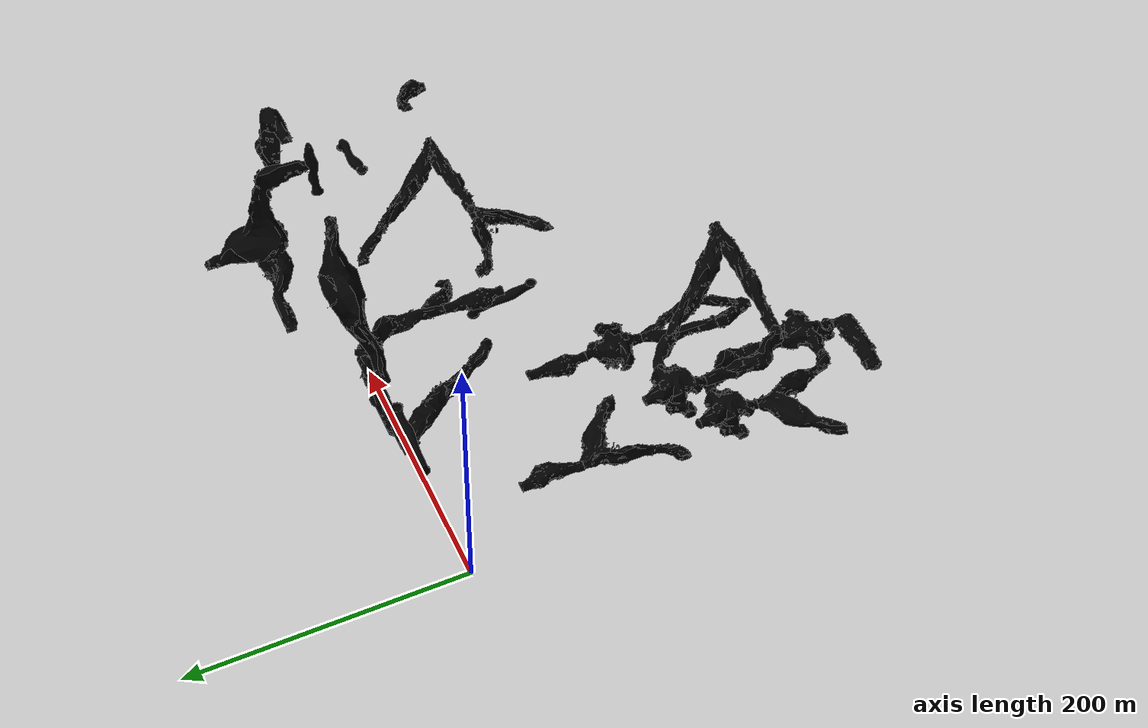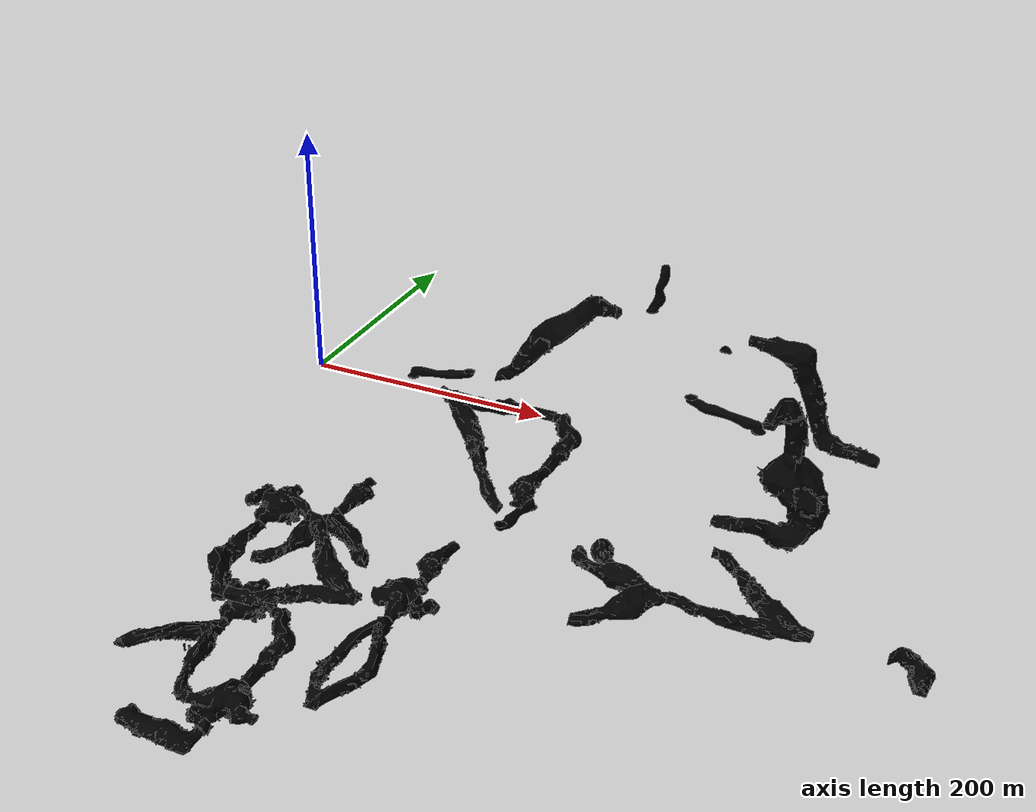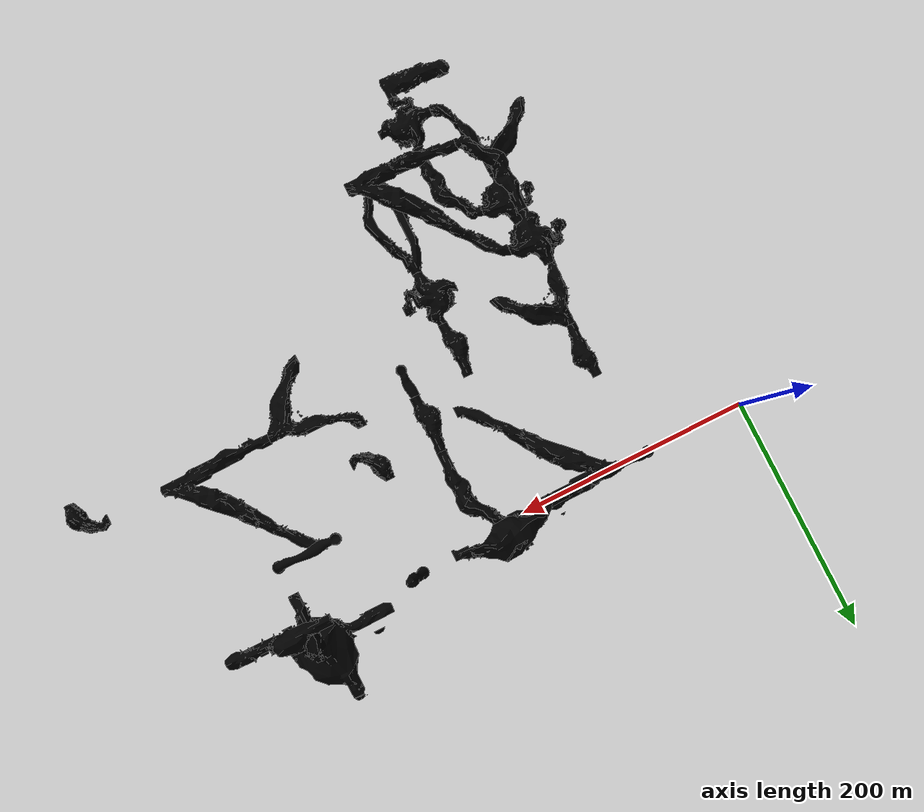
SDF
<sdf version="1.6">
 <world name="cave_circuit_07">
  <physics name="1ms" type="ode">
   <max_step_size>0.004</max_step_size>
   <real_time_factor>1.0</real_time_factor>
  </physics>
  <scene>
   <ambient>0.1 0.1 0.1 1.0</ambient>
   <background>0 0 0 1.0</background>
   <grid>false</grid>
   <origin_visual>false</origin_visual>
  </scene>
  <atmosphere type="adiabatic">
   <temperature>288</temperature>
   <temperature_gradient>0.2</temperature_gradient>
  </atmosphere>
  <model name="performer_detector_rockfall_1">
   <static>true</static>
   <pose>297.5 -203 -26 0 0 0</pose>
   <plugin filename="libignition-gazebo-performer-detector-system.so" name="ignition::gazebo::systems::PerformerDetector">
    <topic>/subt_performer_detector</topic>
    <geometry><box><size>16 16 16</size></box></geometry>
   </plugin>
   <plugin name="ignition::gazebo::systems::TriggeredPublisher" filename="libignition-gazebo-triggered-publisher-system.so">
    <input type="ignition.msgs.Pose" topic="/subt_performer_detector">
     <match field="header.data">{ key: "frame_id" value: "performer_detector_rockfall_1" }</match>
     <match field="header.data">{ key: "state" value: "1" }</match>
    </input>
    <output type="ignition.msgs.Empty" topic="/model/dynamic_rocks_1/breadcrumbs/Rock/deploy"/>
   </plugin>
  </model>
  <model name="performer_detector_rockfall_2">
   <static>true</static>
   <pose>116.193000 -199.961000 -0.159720 0 0 0</pose>
   <plugin filename="libignition-gazebo-performer-detector-system.so" name="ignition::gazebo::systems::PerformerDetector">
    <topic>/subt_performer_detector</topic>
    <geometry><box><size>16 16 15</size></box></geometry>
   </plugin>
   <plugin name="ignition::gazebo::systems::TriggeredPublisher" filename="libignition-gazebo-triggered-publisher-system.so">
    <input type="ignition.msgs.Pose" topic="/subt_performer_detector">
     <match field="header.data">{ key: "frame_id" value: "performer_detector_rockfall_2" }</match>
     <match field="header.data">{ key: "state" value: "0" }</match>
    </input>
    <output type="ignition.msgs.Empty" topic="/model/dynamic_rocks_2/breadcrumbs/Rock/deploy"/>
   </plugin>
  </model>
  <model name="performer_detector_rockfall_3">
   <static>true</static>
   <pose>206.000000 -285.211000 -47.650000 0 0 0</pose>
   <plugin filename="libignition-gazebo-performer-detector-system.so" name="ignition::gazebo::systems::PerformerDetector">
    <topic>/subt_performer_detector</topic>
    <geometry><box><size>16 16 15</size></box></geometry>
   </plugin>
   <plugin name="ignition::gazebo::systems::TriggeredPublisher" filename="libignition-gazebo-triggered-publisher-system.so">
    <input type="ignition.msgs.Pose" topic="/subt_performer_detector">
     <match field="header.data">{ key: "frame_id" value: "performer_detector_rockfall_3" }</match>
     <match field="header.data">{ key: "state" value: "0" }</match>
    </input>
    <output type="ignition.msgs.Empty" topic="/model/dynamic_rocks_3/breadcrumbs/Rock/deploy"/>
   </plugin>
  </model>
  <include>
   <pose>162.5 -300.0 25.0 0.0 0.0 -1.5708</pose>
   <uri>https://fuel.ignitionrobotics.org/1.0/OpenRobotics/models/Cave 3 Way Elevation 01 Type A</uri>
   <name>tile_3</name>
  </include>
  <include>
   <pose>187.5 -200.0 -50.0 0.0 0.0 -1.5708</pose>
   <uri>https://fuel.ignitionrobotics.org/1.0/OpenRobotics/models/Cave 4 Way 01 Type A</uri>
   <name>tile_4</name>
  </include>
  <include>
   <pose>87.5 -250.0 -50.0 0.0 0.0 1.5708</pose>
   <uri>https://fuel.ignitionrobotics.org/1.0/OpenRobotics/models/Cave 4 Way 01 Type A</uri>
   <name>tile_5</name>
  </include>
  <include>
   <pose>87.5 -200.0 0.0 0.0 0.0 1.5708</pose>
   <uri>https://fuel.ignitionrobotics.org/1.0/OpenRobotics/models/Cave 4 Way 01 Type A</uri>
   <name>tile_7</name>
  </include>
  <include>
   <pose>87.5 -150.0 -50.0 0.0 0.0 -3.14159</pose>
   <uri>https://fuel.ignitionrobotics.org/1.0/OpenRobotics/models/Cave 3 Way 02 Type A</uri>
   <name>tile_9</name>
  </include>
  <include>
   <pose>87.5 -100.0 -50.0 0.0 0.0 0.0</pose>
   <uri>https://fuel.ignitionrobotics.org/1.0/OpenRobotics/models/Cave Straight Type A</uri>
   <name>tile_12</name>
  </include>
  <include>
   <pose>337.5 -150.0 -25.0 0.0 0.0 1.5708</pose>
   <uri>https://fuel.ignitionrobotics.org/1.0/OpenRobotics/models/Cave 3 Way 02 Type A</uri>
   <name>tile_14</name>
  </include>
  <include>
   <pose>237.5 -100.0 -25.0 0.0 0.0 -3.14159</pose>
   <uri>https://fuel.ignitionrobotics.org/1.0/OpenRobotics/models/Cave Vertical Shaft Cantilevered Type A</uri>
   <name>tile_18</name>
  </include>
  <include>
   <pose>162.5 0.0 0.0 0.0 0.0 1.5708</pose>
   <uri>https://fuel.ignitionrobotics.org/1.0/OpenRobotics/models/Cave 3 Way Elevation 02 Lights Type A</uri>
   <name>tile_19</name>
  </include>
  <include>
   <pose>412.5 -150.0 -25.0 0.0 0.0 -1.5708</pose>
   <uri>https://fuel.ignitionrobotics.org/1.0/OpenRobotics/models/Cave 3 Way Elevation 02 Type A</uri>
   <name>tile_20</name>
  </include>
  <include>
   <pose>87.5 -300.0 -50.0 0.0 0.0 -3.14159</pose>
   <uri>https://fuel.ignitionrobotics.org/1.0/OpenRobotics/models/Cave 3 Way 01 Type A</uri>
   <name>tile_22</name>
  </include>
  <include>
   <pose>112.5 -375.0 -50.0 0.0 0.0 -3.14159</pose>
   <uri>https://fuel.ignitionrobotics.org/1.0/OpenRobotics/models/Cave 2 Way 01 Type A</uri>
   <name>tile_24</name>
  </include>
  <include>
   <pose>137.5 -350.0 -50.0 0.0 0.0 3.14159</pose>
   <uri>https://fuel.ignitionrobotics.org/1.0/OpenRobotics/models/Cave 4 Way 01 Type A</uri>
   <name>tile_25</name>
  </include>
  <include>
   <pose>187.5 -275.0 -50.0 0.0 0.0 -3.14159</pose>
   <uri>https://fuel.ignitionrobotics.org/1.0/OpenRobotics/models/Cave Split Type A</uri>
   <name>tile_26</name>
  </include>
  <include>
   <pose>137.5 -300.0 -50.0 0.0 0.0 -3.14159</pose>
   <uri>https://fuel.ignitionrobotics.org/1.0/OpenRobotics/models/Cave Corner 02 Type A</uri>
   <name>tile_28</name>
  </include>
  <include>
   <pose>87.5 -250.0 0.0 0.0 0.0 0.0</pose>
   <uri>https://fuel.ignitionrobotics.org/1.0/OpenRobotics/models/Cave Corner 02 Type A</uri>
   <name>tile_29</name>
  </include>
  <include>
   <pose>87.5 0.0 0.0 0.0 0.0 -1.5708</pose>
   <uri>https://fuel.ignitionrobotics.org/1.0/OpenRobotics/models/Cave Vertical Shaft Cantilevered Type A</uri>
   <name>tile_31</name>
  </include>
  <include>
   <pose>187.5 -150.0 -50.0 0.0 0.0 -3.14159</pose>
   <uri>https://fuel.ignitionrobotics.org/1.0/OpenRobotics/models/Cave Straight Type A</uri>
   <name>tile_34</name>
  </include>
  <include>
   <pose>237.5 -50.0 0.0 0.0 0.0 -3.14159</pose>
   <uri>https://fuel.ignitionrobotics.org/1.0/OpenRobotics/models/Cave Corner 02 Lights Type A</uri>
   <name>tile_35</name>
  </include>
  <include>
   <pose>237.5 -100.0 0.0 0.0 0.0 -3.14159</pose>
   <uri>https://fuel.ignitionrobotics.org/1.0/OpenRobotics/models/Cave Straight Type A</uri>
   <name>tile_36</name>
  </include>
  <include>
   <pose>287.5 -100.0 -50.0 0.0 0.0 -3.14159</pose>
   <uri>https://fuel.ignitionrobotics.org/1.0/OpenRobotics/models/Cave Corner 03 Type A</uri>
   <name>tile_38</name>
  </include>
  <include>
   <pose>387.5 -50.0 50.0 0.0 0.0 1.5707</pose>
   <uri>https://fuel.ignitionrobotics.org/1.0/OpenRobotics/models/Cave Vertical Shaft Cantilevered Type A</uri>
   <name>tile_40</name>
  </include>
  <include>
   <pose>412.5 0.0 25.0 0.0 0.0 1.5708</pose>
   <uri>https://fuel.ignitionrobotics.org/1.0/OpenRobotics/models/Cave Elevation 01 Type A</uri>
   <name>tile_45</name>
  </include>
  <include>
   <pose>537.5 -150.0 -25.0 0.0 0.0 0.0</pose>
   <uri>https://fuel.ignitionrobotics.org/1.0/OpenRobotics/models/Cave Corner 03 Type A</uri>
   <name>tile_51</name>
  </include>
  <include>
   <pose>212.499984701 0.0 25.0 0.0 0.0 -3.14159</pose>
   <uri>https://fuel.ignitionrobotics.org/1.0/OpenRobotics/models/Cave Elevation 02 Type A</uri>
   <name>tile_53</name>
  </include>
  <include>
   <pose>287.5 0.0 100.0 0.0 0.0 -1.5708</pose>
   <uri>https://fuel.ignitionrobotics.org/1.0/OpenRobotics/models/Cave Vertical Shaft Dead End Type A</uri>
   <name>tile_55</name>
  </include>
  <include>
   <pose>387.5 25.0 -25.0 0.0 0.0 -3.14159</pose>
   <uri>https://fuel.ignitionrobotics.org/1.0/OpenRobotics/models/Cave 3 Way Elevation 03 Type A</uri>
   <name>tile_56</name>
  </include>
  <include>
   <pose>62.5 -200.0 0.0 0.0 0.0 1.5708</pose>
   <uri>https://fuel.ignitionrobotics.org/1.0/OpenRobotics/models/Cave Cap Type A</uri>
   <name>cap_100</name>
  </include>
  <include>
   <pose>337.5 25.0 75.0 0.0 0.0 0.0</pose>
   <uri>https://fuel.ignitionrobotics.org/1.0/OpenRobotics/models/Cave Cap Type A</uri>
   <name>cap_101</name>
  </include>
  <include>
   <pose>387.5 75.0 -25.0 0.0 0.0 0.0</pose>
   <uri>https://fuel.ignitionrobotics.org/1.0/OpenRobotics/models/Cave Cap Type A</uri>
   <name>cap_102</name>
  </include>
  <include>
   <pose>87.5 -225.0 -50.0 0.0 0.0 0.0</pose>
   <uri>https://fuel.ignitionrobotics.org/1.0/OpenRobotics/models/Cave Cap Type A</uri>
   <name>cap_103</name>
  </include>
  <plugin name="ignition::gazebo" filename="dummy">
   <level name="level0">
    <ref>tile_1</ref>
    <ref>tile_21</ref>
    <pose>37.5 -150 28.279 0 0 0</pose>
    <geometry><box><size>189.375 810 474.558</size></box></geometry>
    <buffer>10</buffer>
   </level>
   <level name="level1">
    <ref>rope_3</ref>
    <pose>37.9176 -150 28.279 0 0 0</pose>
    <geometry><box><size>189.375 810 474.558</size></box></geometry>
    <buffer>10</buffer>
   </level>
   <level name="level2">
    <ref>phone_3</ref>
    <pose>44.57 -150 28.279 0 0 0</pose>
    <geometry><box><size>189.375 810 474.558</size></box></geometry>
    <buffer>10</buffer>
   </level>
   <level name="level3">
    <ref>tile_23</ref>
    <ref>cap_100</ref>
    <pose>62.5 -150 28.279 0 0 0</pose>
    <geometry><box><size>189.375 810 474.558</size></box></geometry>
    <buffer>10</buffer>
   </level>
   <level name="level4">
    <ref>helmet_1</ref>
    <pose>86.842 -150 28.279 0 0 0</pose>
    <geometry><box><size>189.375 810 474.558</size></box></geometry>
    <buffer>10</buffer>
   </level>
   <level name="level5">
    <ref>tile_5</ref>
    <ref>tile_7</ref>
    <ref>tile_9</ref>
    <ref>tile_12</ref>
    <ref>tile_22</ref>
    <ref>tile_29</ref>
    <ref>tile_30</ref>
    <ref>tile_31</ref>
    <ref>tile_32</ref>
    <ref>cap_103</ref>
    <pose>87.5 -150 28.279 0 0 0</pose>
    <geometry><box><size>189.375 810 474.558</size></box></geometry>
    <buffer>10</buffer>
   </level>
   <level name="level6">
    <ref>backpack_3</ref>
    <pose>95.651 -150 28.279 0 0 0</pose>
    <geometry><box><size>189.375 810 474.558</size></box></geometry>
    <buffer>10</buffer>
   </level>
   <level name="level7">
    <ref>rescue_randy_1</ref>
    <pose>99.7389 -150 28.279 0 0 0</pose>
    <geometry><box><size>189.375 810 474.558</size></box></geometry>
    <buffer>10</buffer>
   </level>
   <level name="level8">
    <ref>tile_10</ref>
    <ref>tile_24</ref>
    <pose>112.5 -150 28.279 0 0 0</pose>
    <geometry><box><size>189.375 810 474.558</size></box></geometry>
    <buffer>10</buffer>
   </level>
   <level name="level9">
    <ref>tile_6</ref>
    <ref>tile_25</ref>
    <ref>tile_28</ref>
    <ref>tile_33</ref>
    <pose>137.5 -150 28.279 0 0 0</pose>
    <geometry><box><size>189.375 810 474.558</size></box></geometry>
    <buffer>10</buffer>
   </level>
   <level name="level10">
    <ref>backpack_1</ref>
    <pose>137.575 -150 28.279 0 0 0</pose>
    <geometry><box><size>189.375 810 474.558</size></box></geometry>
    <buffer>10</buffer>
   </level>
   <level name="level11">
    <ref>tile_3</ref>
    <ref>tile_11</ref>
    <ref>tile_19</ref>
    <pose>162.5 -150 28.279 0 0 0</pose>
    <geometry><box><size>189.375 810 474.558</size></box></geometry>
    <buffer>10</buffer>
   </level>
   <level name="level12">
    <ref>backpack_4</ref>
    <pose>175.098 -150 28.279 0 0 0</pose>
    <geometry><box><size>189.375 810 474.558</size></box></geometry>
    <buffer>10</buffer>
   </level>
   <level name="level13">
    <ref>rope_2</ref>
    <pose>176.192 -150 28.279 0 0 0</pose>
    <geometry><box><size>189.375 810 474.558</size></box></geometry>
    <buffer>10</buffer>
   </level>
   <level name="level14">
    <ref>helmet_2</ref>
    <pose>180.66 -150 28.279 0 0 0</pose>
    <geometry><box><size>189.375 810 474.558</size></box></geometry>
    <buffer>10</buffer>
   </level>
   <level name="level15">
    <ref>phone_2</ref>
    <pose>184.744 -150 28.279 0 0 0</pose>
    <geometry><box><size>189.375 810 474.558</size></box></geometry>
    <buffer>10</buffer>
   </level>
   <level name="level16">
    <ref>backpack_2</ref>
    <pose>185.172 -150 28.279 0 0 0</pose>
    <geometry><box><size>189.375 810 474.558</size></box></geometry>
    <buffer>10</buffer>
   </level>
   <level name="level17">
    <ref>tile_4</ref>
    <ref>tile_26</ref>
    <ref>tile_27</ref>
    <ref>tile_34</ref>
    <pose>187.5 -150 28.279 0 0 0</pose>
    <geometry><box><size>189.375 810 474.558</size></box></geometry>
    <buffer>10</buffer>
   </level>
   <level name="level18">
    <ref>rescue_randy_2</ref>
    <pose>194.299 -150 28.279 0 0 0</pose>
    <geometry><box><size>189.375 810 474.558</size></box></geometry>
    <buffer>10</buffer>
   </level>
   <level name="level19">
    <ref>tile_53</ref>
    <pose>212.5 -150 28.279 0 0 0</pose>
    <geometry><box><size>189.375 810 474.558</size></box></geometry>
    <buffer>10</buffer>
   </level>
   <level name="level20">
    <ref>tile_2</ref>
    <ref>tile_8</ref>
    <ref>tile_16</ref>
    <ref>tile_17</ref>
    <ref>tile_18</ref>
    <ref>tile_35</ref>
    <ref>tile_36</ref>
    <pose>237.5 -150 28.279 0 0 0</pose>
    <geometry><box><size>189.375 810 474.558</size></box></geometry>
    <buffer>10</buffer>
   </level>
   <level name="level21">
    <ref>tile_13</ref>
    <pose>262.5 -150 28.279 0 0 0</pose>
    <geometry><box><size>189.375 810 474.558</size></box></geometry>
    <buffer>10</buffer>
   </level>
   <level name="level22">
    <ref>tile_15</ref>
    <ref>tile_38</ref>
    <ref>tile_39</ref>
    <ref>tile_54</ref>
    <ref>tile_55</ref>
    <ref>phone_1</ref>
    <pose>287.5 -150 28.279 0 0 0</pose>
    <geometry><box><size>189.375 810 474.558</size></box></geometry>
    <buffer>10</buffer>
   </level>
   <level name="level23">
    <ref>rescue_randy_3</ref>
    <pose>293.153 -150 28.279 0 0 0</pose>
    <geometry><box><size>189.375 810 474.558</size></box></geometry>
    <buffer>10</buffer>
   </level>
   <level name="level24">
    <ref>helmet_4</ref>
    <pose>296.8 -150 28.279 0 0 0</pose>
    <geometry><box><size>189.375 810 474.558</size></box></geometry>
    <buffer>10</buffer>
   </level>
   <level name="level25">
    <ref>tile_14</ref>
    <ref>tile_37</ref>
    <ref>tile_42</ref>
    <ref>tile_43</ref>
    <ref>tile_44</ref>
    <ref>cap_101</ref>
    <pose>337.5 -150 28.279 0 0 0</pose>
    <geometry><box><size>189.375 810 474.558</size></box></geometry>
    <buffer>10</buffer>
   </level>
   <level name="level26">
    <ref>rescue_randy_4</ref>
    <pose>384.628 -150 28.279 0 0 0</pose>
    <geometry><box><size>189.375 810 474.558</size></box></geometry>
    <buffer>10</buffer>
   </level>
   <level name="level27">
    <ref>tile_40</ref>
    <ref>tile_41</ref>
    <ref>tile_56</ref>
    <ref>cap_102</ref>
    <pose>387.5 -150 28.279 0 0 0</pose>
    <geometry><box><size>189.375 810 474.558</size></box></geometry>
    <buffer>10</buffer>
   </level>
   <level name="level28">
    <ref>rope_4</ref>
    <pose>409.12 -150 28.279 0 0 0</pose>
    <geometry><box><size>189.375 810 474.558</size></box></geometry>
    <buffer>10</buffer>
   </level>
   <level name="level29">
    <ref>phone_4</ref>
    <pose>412.14 -150 28.279 0 0 0</pose>
    <geometry><box><size>189.375 810 474.558</size></box></geometry>
    <buffer>10</buffer>
   </level>
   <level name="level30">
    <ref>tile_20</ref>
    <ref>tile_45</ref>
    <pose>412.5 -150 28.279 0 0 0</pose>
    <geometry><box><size>189.375 810 474.558</size></box></geometry>
    <buffer>10</buffer>
   </level>
   <level name="level31">
    <ref>helmet_3</ref>
    <pose>467.135 -150 28.279 0 0 0</pose>
    <geometry><box><size>189.375 810 474.558</size></box></geometry>
    <buffer>10</buffer>
   </level>
   <level name="level32">
    <ref>rope_1</ref>
    <pose>482.715 -150 28.279 0 0 0</pose>
    <geometry><box><size>189.375 810 474.558</size></box></geometry>
    <buffer>10</buffer>
   </level>
   <level name="level33">
    <ref>tile_46</ref>
    <ref>tile_47</ref>
    <ref>tile_48</ref>
    <ref>tile_49</ref>
    <ref>tile_50</ref>
    <ref>tile_52</ref>
    <pose>487.5 -150 28.279 0 0 0</pose>
    <geometry><box><size>189.375 810 474.558</size></box></geometry>
    <buffer>10</buffer>
   </level>
   <level name="level34">
    <ref>tile_51</ref>
    <pose>537.5 -150 28.279 0 0 0</pose>
    <geometry><box><size>189.375 810 474.558</size></box></geometry>
    <buffer>10</buffer>
   </level>
   <level name="level35">
    <ref>tile_24</ref>
    <pose>287.5 -375 28.279 0 0 0</pose>
    <geometry><box><size>702 337.5 474.558</size></box></geometry>
    <buffer>10</buffer>
   </level>
   <level name="level36">
    <ref>tile_23</ref>
    <ref>tile_25</ref>
    <ref>tile_27</ref>
    <pose>287.5 -350 28.279 0 0 0</pose>
    <geometry><box><size>702 337.5 474.558</size></box></geometry>
    <buffer>10</buffer>
   </level>
   <level name="level37">
    <ref>rope_2</ref>
    <pose>287.5 -348.321 28.279 0 0 0</pose>
    <geometry><box><size>702 337.5 474.558</size></box></geometry>
    <buffer>10</buffer>
   </level>
   <level name="level38">
    <ref>phone_3</ref>
    <pose>287.5 -335.853 28.279 0 0 0</pose>
    <geometry><box><size>702 337.5 474.558</size></box></geometry>
    <buffer>10</buffer>
   </level>
   <level name="level39">
    <ref>tile_2</ref>
    <ref>tile_3</ref>
    <ref>tile_22</ref>
    <ref>tile_28</ref>
    <pose>287.5 -300 28.279 0 0 0</pose>
    <geometry><box><size>702 337.5 474.558</size></box></geometry>
    <buffer>10</buffer>
   </level>
   <level name="level40">
    <ref>tile_26</ref>
    <pose>287.5 -275 28.279 0 0 0</pose>
    <geometry><box><size>702 337.5 474.558</size></box></geometry>
    <buffer>10</buffer>
   </level>
   <level name="level41">
    <ref>tile_5</ref>
    <ref>tile_29</ref>
    <pose>287.5 -250 28.279 0 0 0</pose>
    <geometry><box><size>702 337.5 474.558</size></box></geometry>
    <buffer>10</buffer>
   </level>
   <level name="level42">
    <ref>helmet_2</ref>
    <pose>287.5 -248.778 28.279 0 0 0</pose>
    <geometry><box><size>702 337.5 474.558</size></box></geometry>
    <buffer>10</buffer>
   </level>
   <level name="level43">
    <ref>backpack_3</ref>
    <pose>287.5 -247.678 28.279 0 0 0</pose>
    <geometry><box><size>702 337.5 474.558</size></box></geometry>
    <buffer>10</buffer>
   </level>
   <level name="level44">
    <ref>rope_3</ref>
    <pose>287.5 -230.892 28.279 0 0 0</pose>
    <geometry><box><size>702 337.5 474.558</size></box></geometry>
    <buffer>10</buffer>
   </level>
   <level name="level45">
    <ref>tile_8</ref>
    <ref>tile_21</ref>
    <ref>cap_103</ref>
    <pose>287.5 -225 28.279 0 0 0</pose>
    <geometry><box><size>702 337.5 474.558</size></box></geometry>
    <buffer>10</buffer>
   </level>
   <level name="level46">
    <ref>tile_4</ref>
    <ref>tile_6</ref>
    <ref>tile_7</ref>
    <ref>tile_13</ref>
    <ref>tile_50</ref>
    <ref>cap_100</ref>
    <pose>287.5 -200 28.279 0 0 0</pose>
    <geometry><box><size>702 337.5 474.558</size></box></geometry>
    <buffer>10</buffer>
   </level>
   <level name="level47">
    <ref>rescue_randy_3</ref>
    <pose>287.5 -196.5 28.279 0 0 0</pose>
    <geometry><box><size>702 337.5 474.558</size></box></geometry>
    <buffer>10</buffer>
   </level>
   <level name="level48">
    <ref>tile_9</ref>
    <ref>tile_14</ref>
    <ref>tile_17</ref>
    <ref>tile_20</ref>
    <ref>tile_34</ref>
    <ref>tile_48</ref>
    <ref>tile_49</ref>
    <ref>tile_51</ref>
    <ref>tile_52</ref>
    <ref>backpack_2</ref>
    <pose>287.5 -150 28.279 0 0 0</pose>
    <geometry><box><size>702 337.5 474.558</size></box></geometry>
    <buffer>10</buffer>
   </level>
   <level name="level49">
    <ref>helmet_3</ref>
    <pose>287.5 -147.069 28.279 0 0 0</pose>
    <geometry><box><size>702 337.5 474.558</size></box></geometry>
    <buffer>10</buffer>
   </level>
   <level name="level50">
    <ref>rescue_randy_1</ref>
    <pose>287.5 -136.003 28.279 0 0 0</pose>
    <geometry><box><size>702 337.5 474.558</size></box></geometry>
    <buffer>10</buffer>
   </level>
   <level name="level51">
    <ref>tile_11</ref>
    <ref>tile_12</ref>
    <ref>tile_15</ref>
    <ref>tile_16</ref>
    <ref>tile_18</ref>
    <ref>tile_36</ref>
    <ref>tile_38</ref>
    <ref>tile_43</ref>
    <pose>287.5 -100 28.279 0 0 0</pose>
    <geometry><box><size>702 337.5 474.558</size></box></geometry>
    <buffer>10</buffer>
   </level>
   <level name="level52">
    <ref>rescue_randy_2</ref>
    <pose>287.5 -82.8494 28.279 0 0 0</pose>
    <geometry><box><size>702 337.5 474.558</size></box></geometry>
    <buffer>10</buffer>
   </level>
   <level name="level53">
    <ref>tile_30</ref>
    <ref>tile_37</ref>
    <ref>tile_47</ref>
    <pose>287.5 -75 28.279 0 0 0</pose>
    <geometry><box><size>702 337.5 474.558</size></box></geometry>
    <buffer>10</buffer>
   </level>
   <level name="level54">
    <ref>tile_10</ref>
    <ref>tile_35</ref>
    <ref>tile_40</ref>
    <ref>tile_41</ref>
    <ref>tile_42</ref>
    <pose>287.5 -50 28.279 0 0 0</pose>
    <geometry><box><size>702 337.5 474.558</size></box></geometry>
    <buffer>10</buffer>
   </level>
   <level name="level55">
    <ref>tile_39</ref>
    <pose>287.5 -25 28.279 0 0 0</pose>
    <geometry><box><size>702 337.5 474.558</size></box></geometry>
    <buffer>10</buffer>
   </level>
   <level name="level56">
    <ref>rescue_randy_4</ref>
    <pose>287.5 -17.2074 28.279 0 0 0</pose>
    <geometry><box><size>702 337.5 474.558</size></box></geometry>
    <buffer>10</buffer>
   </level>
   <level name="level57">
    <ref>helmet_1</ref>
    <pose>287.5 -15.166 28.279 0 0 0</pose>
    <geometry><box><size>702 337.5 474.558</size></box></geometry>
    <buffer>10</buffer>
   </level>
   <level name="level58">
    <ref>phone_2</ref>
    <pose>287.5 -1.57987 28.279 0 0 0</pose>
    <geometry><box><size>702 337.5 474.558</size></box></geometry>
    <buffer>10</buffer>
   </level>
   <level name="level59">
    <ref>helmet_4</ref>
    <pose>287.5 -0.13845 28.279 0 0 0</pose>
    <geometry><box><size>702 337.5 474.558</size></box></geometry>
    <buffer>10</buffer>
   </level>
   <level name="level60">
    <ref>tile_1</ref>
    <ref>tile_19</ref>
    <ref>tile_31</ref>
    <ref>tile_32</ref>
    <ref>tile_33</ref>
    <ref>tile_44</ref>
    <ref>tile_45</ref>
    <ref>tile_46</ref>
    <ref>tile_53</ref>
    <ref>tile_54</ref>
    <ref>tile_55</ref>
    <pose>287.5 0 28.279 0 0 0</pose>
    <geometry><box><size>702 337.5 474.558</size></box></geometry>
    <buffer>10</buffer>
   </level>
   <level name="level61">
    <ref>rope_1</ref>
    <pose>287.5 1.36702 28.279 0 0 0</pose>
    <geometry><box><size>702 337.5 474.558</size></box></geometry>
    <buffer>10</buffer>
   </level>
   <level name="level62">
    <ref>backpack_4</ref>
    <pose>287.5 2.35599 28.279 0 0 0</pose>
    <geometry><box><size>702 337.5 474.558</size></box></geometry>
    <buffer>10</buffer>
   </level>
   <level name="level63">
    <ref>rope_4</ref>
    <pose>287.5 3.43221 28.279 0 0 0</pose>
    <geometry><box><size>702 337.5 474.558</size></box></geometry>
    <buffer>10</buffer>
   </level>
   <level name="level64">
    <ref>backpack_1</ref>
    <pose>287.5 3.74603 28.279 0 0 0</pose>
    <geometry><box><size>702 337.5 474.558</size></box></geometry>
    <buffer>10</buffer>
   </level>
   <level name="level65">
    <ref>phone_1</ref>
    <pose>287.5 15.5 28.279 0 0 0</pose>
    <geometry><box><size>702 337.5 474.558</size></box></geometry>
    <buffer>10</buffer>
   </level>
   <level name="level66">
    <ref>phone_4</ref>
    <pose>287.5 22.825 28.279 0 0 0</pose>
    <geometry><box><size>702 337.5 474.558</size></box></geometry>
    <buffer>10</buffer>
   </level>
   <level name="level67">
    <ref>tile_56</ref>
    <ref>cap_101</ref>
    <pose>287.5 25 28.279 0 0 0</pose>
    <geometry><box><size>702 337.5 474.558</size></box></geometry>
    <buffer>10</buffer>
   </level>
   <level name="level68">
    <ref>cap_102</ref>
    <pose>287.5 75 28.279 0 0 0</pose>
    <geometry><box><size>702 337.5 474.558</size></box></geometry>
    <buffer>10</buffer>
   </level>
  </plugin>
 </world>
</sdf>

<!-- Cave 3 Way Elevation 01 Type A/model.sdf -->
<sdf version="1.6">
  <model name="Cave 3 Way Elevation 01 Type A">
    <static>true</static>
    <link name="base_link">
      <collision name="collision">
        <pose>0 0 0 0 0 0</pose>
        <geometry>
          <mesh>
            <uri>model://Cave 3 Way Elevation 01 Type A/meshes/3wayelevation01.dae</uri>
            <scale>1.0 1.0 1.0</scale>
          </mesh>
        </geometry>
      </collision>
      <visual name="CaveWall_visual">
        <geometry>
          <mesh>
            <uri>model://Cave 3 Way Elevation 01 Type A/meshes/3wayelevation01.dae</uri>
            <submesh>
              <name>CaveWall</name>
              <center>false</center>
            </submesh>
          </mesh>
        </geometry>
        <material>
          <diffuse>0 0 0 1</diffuse>
          <specular>0 0 0 1</specular>
          <pbr>
            <metal>
              <albedo_map>model://Cave 3 Way Elevation 01 Type A/materials/textures/CaveWall_Albedo.png</albedo_map>
              <normal_map>model://Cave 3 Way Elevation 01 Type A/materials/textures/CaveWall_Normal.png</normal_map>
              <roughness_map>model://Cave 3 Way Elevation 01 Type A/materials/textures/CaveWall_Roughness.png</roughness_map>
            </metal>
          </pbr>

          <script>
            <uri>model://Cave 3 Way Elevation 01 Type A/materials/scripts/</uri>
            <uri>model://Cave 3 Way Elevation 01 Type A/materials/textures/</uri>
            <name>CaveTile/CaveWall_Diffuse</name>
          </script>
        </material>
      </visual>
      <visual name="Gravel_visual">
        <geometry>
          <mesh>
            <uri>model://Cave 3 Way Elevation 01 Type A/meshes/3wayelevation01.dae</uri>
            <submesh>
              <name>Gravel</name>
              <center>false</center>
            </submesh>
          </mesh>
        </geometry>
        <material>
          <diffuse>0 0 0 1</diffuse>
          <specular>0 0 0 1</specular>
          <pbr>
            <metal>
              <albedo_map>model://Cave 3 Way Elevation 01 Type A/materials/textures/Gravel_Albedo.png</albedo_map>
              <normal_map>model://Cave 3 Way Elevation 01 Type A/materials/textures/Gravel_Normal.png</normal_map>
              <roughness_map>model://Cave 3 Way Elevation 01 Type A/materials/textures/Gravel_Roughness.png</roughness_map>
            </metal>
          </pbr>

          <script>
            <uri>model://Cave 3 Way Elevation 01 Type A/materials/scripts/</uri>
            <uri>model://Cave 3 Way Elevation 01 Type A/materials/textures/</uri>
            <name>CaveTile/Gravel_Diffuse</name>
          </script>
        </material>
      </visual>
      <visual name="StriatedRock_visual">
        <geometry>
          <mesh>
            <uri>model://Cave 3 Way Elevation 01 Type A/meshes/3wayelevation01.dae</uri>
            <submesh>
              <name>StriatedRock</name>
              <center>false</center>
            </submesh>
          </mesh>
        </geometry>
        <material>
          <diffuse>0 0 0 1</diffuse>
          <specular>0 0 0 1</specular>
          <pbr>
            <metal>
              <albedo_map>model://Cave 3 Way Elevation 01 Type A/materials/textures/StriatedRock_Albedo.png</albedo_map>
              <normal_map>model://Cave 3 Way Elevation 01 Type A/materials/textures/StriatedRock_Normal.png</normal_map>
              <roughness_map>model://Cave 3 Way Elevation 01 Type A/materials/textures/StriatedRock_Roughness.png</roughness_map>
            </metal>
          </pbr>

          <script>
            <uri>model://Cave 3 Way Elevation 01 Type A/materials/scripts/</uri>
            <uri>model://Cave 3 Way Elevation 01 Type A/materials/textures/</uri>
            <name>CaveTile/StriatedRock_Diffuse</name>
          </script>
        </material>
      </visual>
      <visual name="RockPile_visual">
        <geometry>
          <mesh>
            <uri>model://Cave 3 Way Elevation 01 Type A/meshes/3wayelevation01.dae</uri>
            <submesh>
              <name>RockPile</name>
              <center>false</center>
            </submesh>
          </mesh>
        </geometry>
        <material>
          <diffuse>0 0 0 1</diffuse>
          <specular>0 0 0 1</specular>
          <pbr>
            <metal>
              <albedo_map>model://Cave 3 Way Elevation 01 Type A/materials/textures/RockPile_Albedo.png</albedo_map>
              <normal_map>model://Cave 3 Way Elevation 01 Type A/materials/textures/RockPile_Normal.png</normal_map>
              <roughness_map>model://Cave 3 Way Elevation 01 Type A/materials/textures/RockPile_Roughness.png</roughness_map>
            </metal>
          </pbr>

          <script>
            <uri>model://Cave 3 Way Elevation 01 Type A/materials/scripts/</uri>
            <uri>model://Cave 3 Way Elevation 01 Type A/materials/textures/</uri>
            <name>CaveTile/RockPile_Diffuse</name>
          </script>
        </material>
      </visual>
    </link>

    <plugin filename="libignition-gazebo-performer-detector-system.so" name="ignition::gazebo::systems::PerformerDetector">
      <topic>/subt_performer_detector</topic>
      <pose>-3.2 42.5 1.7 0 0 0</pose>
      <header_data>
        <key>type</key>
        <value>decision</value>
      </header_data>
      <geometry>
        <box>
          <size>15 15 7</size>
        </box>
      </geometry>
    </plugin>
    <plugin filename="libignition-gazebo-performer-detector-system.so" name="ignition::gazebo::systems::PerformerDetector">
      <topic>/subt_performer_detector</topic>
      <pose>-50 0 -6.5 0 0 0</pose>
      <header_data>
        <key>type</key>
        <value>elevation</value>
      </header_data>
      <geometry>
        <box>
          <size>40 40 20</size>
        </box>
      </geometry>
    </plugin>
  </model>
</sdf>

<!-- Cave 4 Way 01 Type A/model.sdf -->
<sdf version="1.6">
  <model name="Cave 4 Way 01 Type A">
    <static>true</static>
    <link name="base_link">
      <collision name="collision">
        <pose>0 0 0 0 0 0</pose>
        <geometry>
          <mesh>
            <uri>model://Cave 4 Way 01 Type A/meshes/4way01.dae</uri>
            <scale>1.0 1.0 1.0</scale>
          </mesh>
        </geometry>
      </collision>
      <visual name="Gravel_visual">
        <geometry>
          <mesh>
            <uri>model://Cave 4 Way 01 Type A/meshes/4way01.dae</uri>
            <submesh>
              <name>Gravel</name>
              <center>false</center>
            </submesh>
          </mesh>
        </geometry>
        <material>
          <diffuse>0 0 0 1</diffuse>
          <specular>0 0 0 1</specular>
          <pbr>
            <metal>
              <albedo_map>model://Cave 4 Way 01 Type A/materials/textures/Gravel_Albedo.png</albedo_map>
              <normal_map>model://Cave 4 Way 01 Type A/materials/textures/Gravel_Normal.png</normal_map>
              <roughness_map>model://Cave 4 Way 01 Type A/materials/textures/Gravel_Roughness.png</roughness_map>
            </metal>
          </pbr>

          <script>
            <uri>model://Cave 4 Way 01 Type A/materials/scripts/</uri>
            <uri>model://Cave 4 Way 01 Type A/materials/textures/</uri>
            <name>CaveTile/Gravel_Diffuse</name>
          </script>
        </material>
      </visual>
      <visual name="RockPile_visual">
        <geometry>
          <mesh>
            <uri>model://Cave 4 Way 01 Type A/meshes/4way01.dae</uri>
            <submesh>
              <name>RockPile</name>
              <center>false</center>
            </submesh>
          </mesh>
        </geometry>
        <material>
          <diffuse>0 0 0 1</diffuse>
          <specular>0 0 0 1</specular>
          <pbr>
            <metal>
              <albedo_map>model://Cave 4 Way 01 Type A/materials/textures/RockPile_Albedo.png</albedo_map>
              <normal_map>model://Cave 4 Way 01 Type A/materials/textures/RockPile_Normal.png</normal_map>
              <roughness_map>model://Cave 4 Way 01 Type A/materials/textures/RockPile_Roughness.png</roughness_map>
            </metal>
          </pbr>

          <script>
            <uri>model://Cave 4 Way 01 Type A/materials/scripts/</uri>
            <uri>model://Cave 4 Way 01 Type A/materials/textures/</uri>
            <name>CaveTile/RockPile_Diffuse</name>
          </script>
        </material>
      </visual>
      <visual name="StriatedRock_visual">
        <geometry>
          <mesh>
            <uri>model://Cave 4 Way 01 Type A/meshes/4way01.dae</uri>
            <submesh>
              <name>StriatedRock</name>
              <center>false</center>
            </submesh>
          </mesh>
        </geometry>
        <material>
          <diffuse>0 0 0 1</diffuse>
          <specular>0 0 0 1</specular>
          <pbr>
            <metal>
              <albedo_map>model://Cave 4 Way 01 Type A/materials/textures/StriatedRock_Albedo.png</albedo_map>
              <normal_map>model://Cave 4 Way 01 Type A/materials/textures/StriatedRock_Normal.png</normal_map>
              <roughness_map>model://Cave 4 Way 01 Type A/materials/textures/StriatedRock_Roughness.png</roughness_map>
            </metal>
          </pbr>

          <script>
            <uri>model://Cave 4 Way 01 Type A/materials/scripts/</uri>
            <uri>model://Cave 4 Way 01 Type A/materials/textures/</uri>
            <name>CaveTile/StriatedRock_Diffuse</name>
          </script>
        </material>
      </visual>
      <visual name="CaveWall_visual">
        <geometry>
          <mesh>
            <uri>model://Cave 4 Way 01 Type A/meshes/4way01.dae</uri>
            <submesh>
              <name>CaveWall</name>
              <center>false</center>
            </submesh>
          </mesh>
        </geometry>
        <material>
          <diffuse>0 0 0 1</diffuse>
          <specular>0 0 0 1</specular>
          <pbr>
            <metal>
              <albedo_map>model://Cave 4 Way 01 Type A/materials/textures/CaveWall_Albedo.png</albedo_map>
              <normal_map>model://Cave 4 Way 01 Type A/materials/textures/CaveWall_Normal.png</normal_map>
              <roughness_map>model://Cave 4 Way 01 Type A/materials/textures/CaveWall_Roughness.png</roughness_map>
            </metal>
          </pbr>

          <script>
            <uri>model://Cave 4 Way 01 Type A/materials/scripts/</uri>
            <uri>model://Cave 4 Way 01 Type A/materials/textures/</uri>
            <name>CaveTile/CaveWall_Diffuse</name>
          </script>
        </material>
      </visual>
    </link>

    <plugin filename="libignition-gazebo-performer-detector-system.so" name="ignition::gazebo::systems::PerformerDetector">
      <topic>/subt_performer_detector</topic>
      <pose>0 -5 5 0 0 0</pose>
      <header_data>
        <key>type</key>
        <value>decision</value>
      </header_data>
      <geometry>
        <box>
          <size>20 20 12</size>
        </box>
      </geometry>
    </plugin>
  </model>
</sdf>

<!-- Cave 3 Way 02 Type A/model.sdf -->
<sdf version="1.6">
  <model name="Cave 3 Way 02 Type A">
    <static>true</static>
    <link name="base_link">
      <collision name="collision">
        <pose>0 0 0 0 0 0</pose>
        <geometry>
          <mesh>
            <uri>model://Cave 3 Way 02 Type A/meshes/3Way02.dae</uri>
            <scale>1.0 1.0 1.0</scale>
          </mesh>
        </geometry>
      </collision>
      <visual name="Gravel_visual">
        <geometry>
          <mesh>
            <uri>model://Cave 3 Way 02 Type A/meshes/3Way02.dae</uri>
            <submesh>
              <name>Gravel</name>
              <center>false</center>
            </submesh>
          </mesh>
        </geometry>
        <material>
          <diffuse>0 0 0 1</diffuse>
          <specular>0 0 0 1</specular>
          <pbr>
            <metal>
              <albedo_map>model://Cave 3 Way 02 Type A/materials/textures/Gravel_Albedo.png</albedo_map>
              <normal_map>model://Cave 3 Way 02 Type A/materials/textures/Gravel_Normal.png</normal_map>
              <roughness_map>model://Cave 3 Way 02 Type A/materials/textures/Gravel_Roughness.png</roughness_map>
            </metal>
          </pbr>

          <script>
            <uri>model://Cave 3 Way 02 Type A/materials/scripts/</uri>
            <uri>model://Cave 3 Way 02 Type A/materials/textures/</uri>
            <name>CaveTile/Gravel_Diffuse</name>
          </script>
        </material>
      </visual>
      <visual name="StriatedRock_visual">
        <geometry>
          <mesh>
            <uri>model://Cave 3 Way 02 Type A/meshes/3Way02.dae</uri>
            <submesh>
              <name>StriatedRock</name>
              <center>false</center>
            </submesh>
          </mesh>
        </geometry>
        <material>
          <diffuse>0 0 0 1</diffuse>
          <specular>0 0 0 1</specular>
          <pbr>
            <metal>
              <albedo_map>model://Cave 3 Way 02 Type A/materials/textures/StriatedRock_Albedo.png</albedo_map>
              <normal_map>model://Cave 3 Way 02 Type A/materials/textures/StriatedRock_Normal.png</normal_map>
              <roughness_map>model://Cave 3 Way 02 Type A/materials/textures/StriatedRock_Roughness.png</roughness_map>
            </metal>
          </pbr>

          <script>
            <uri>model://Cave 3 Way 02 Type A/materials/scripts/</uri>
            <uri>model://Cave 3 Way 02 Type A/materials/textures/</uri>
            <name>CaveTile/StriatedRock_Diffuse</name>
          </script>
        </material>
      </visual>
      <visual name="RockPile_visual">
        <geometry>
          <mesh>
            <uri>model://Cave 3 Way 02 Type A/meshes/3Way02.dae</uri>
            <submesh>
              <name>RockPile</name>
              <center>false</center>
            </submesh>
          </mesh>
        </geometry>
        <material>
          <diffuse>0 0 0 1</diffuse>
          <specular>0 0 0 1</specular>
          <pbr>
            <metal>
              <albedo_map>model://Cave 3 Way 02 Type A/materials/textures/RockPile_Albedo.png</albedo_map>
              <normal_map>model://Cave 3 Way 02 Type A/materials/textures/RockPile_Normal.png</normal_map>
              <roughness_map>model://Cave 3 Way 02 Type A/materials/textures/RockPile_Roughness.png</roughness_map>
            </metal>
          </pbr>

          <script>
            <uri>model://Cave 3 Way 02 Type A/materials/scripts/</uri>
            <uri>model://Cave 3 Way 02 Type A/materials/textures/</uri>
            <name>CaveTile/RockPile_Diffuse</name>
          </script>
        </material>
      </visual>
      <visual name="CaveWall_visual">
        <geometry>
          <mesh>
            <uri>model://Cave 3 Way 02 Type A/meshes/3Way02.dae</uri>
            <submesh>
              <name>CaveWall</name>
              <center>false</center>
            </submesh>
          </mesh>
        </geometry>
        <material>
          <diffuse>0 0 0 1</diffuse>
          <specular>0 0 0 1</specular>
          <pbr>
            <metal>
              <albedo_map>model://Cave 3 Way 02 Type A/materials/textures/CaveWall_Albedo.png</albedo_map>
              <normal_map>model://Cave 3 Way 02 Type A/materials/textures/CaveWall_Normal.png</normal_map>
              <roughness_map>model://Cave 3 Way 02 Type A/materials/textures/CaveWall_Roughness.png</roughness_map>
            </metal>
          </pbr>

          <script>
            <uri>model://Cave 3 Way 02 Type A/materials/scripts/</uri>
            <uri>model://Cave 3 Way 02 Type A/materials/textures/</uri>
            <name>CaveTile/CaveWall_Diffuse</name>
          </script>
        </material>
      </visual>
    </link>
  </model>
</sdf>

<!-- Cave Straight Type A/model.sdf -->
<sdf version="1.6">
  <model name="Cave Straight Type A">
    <static>true</static>
    <link name="base_link">
      <collision name="collision">
        <pose>0 0 0 0 0 0</pose>
        <geometry>
          <mesh>
            <uri>model://Cave Straight Type A/meshes/straight.dae</uri>
            <scale>1.0 1.0 1.0</scale>
          </mesh>
        </geometry>
      </collision>
      <visual name="Gravel_visual">
        <geometry>
          <mesh>
            <uri>model://Cave Straight Type A/meshes/straight.dae</uri>
            <submesh>
              <name>Gravel</name>
              <center>false</center>
            </submesh>
          </mesh>
        </geometry>
        <material>
          <diffuse>0 0 0 1</diffuse>
          <specular>0 0 0 1</specular>
          <pbr>
            <metal>
              <albedo_map>model://Cave Straight Type A/materials/textures/Gravel_Albedo.png</albedo_map>
              <normal_map>model://Cave Straight Type A/materials/textures/Gravel_Normal.png</normal_map>
              <roughness_map>model://Cave Straight Type A/materials/textures/Gravel_Roughness.png</roughness_map>
            </metal>
          </pbr>

          <script>
            <uri>model://Cave Straight Type A/materials/scripts/</uri>
            <uri>model://Cave Straight Type A/materials/textures/</uri>
            <name>CaveTile/Gravel_Diffuse</name>
          </script>
        </material>
      </visual>
      <visual name="RockPile_visual">
        <geometry>
          <mesh>
            <uri>model://Cave Straight Type A/meshes/straight.dae</uri>
            <submesh>
              <name>RockPile</name>
              <center>false</center>
            </submesh>
          </mesh>
        </geometry>
        <material>
          <diffuse>0 0 0 1</diffuse>
          <specular>0 0 0 1</specular>
          <pbr>
            <metal>
              <albedo_map>model://Cave Straight Type A/materials/textures/RockPile_Albedo.png</albedo_map>
              <normal_map>model://Cave Straight Type A/materials/textures/RockPile_Normal.png</normal_map>
              <roughness_map>model://Cave Straight Type A/materials/textures/RockPile_Roughness.png</roughness_map>
            </metal>
          </pbr>

          <script>
            <uri>model://Cave Straight Type A/materials/scripts/</uri>
            <uri>model://Cave Straight Type A/materials/textures/</uri>
            <name>CaveTile/RockPile_Diffuse</name>
          </script>
        </material>
      </visual>
      <visual name="StriatedRock_visual">
        <geometry>
          <mesh>
            <uri>model://Cave Straight Type A/meshes/straight.dae</uri>
            <submesh>
              <name>StriatedRock</name>
              <center>false</center>
            </submesh>
          </mesh>
        </geometry>
        <material>
          <diffuse>0 0 0 1</diffuse>
          <specular>0 0 0 1</specular>
          <pbr>
            <metal>
              <albedo_map>model://Cave Straight Type A/materials/textures/StriatedRock_Albedo.png</albedo_map>
              <normal_map>model://Cave Straight Type A/materials/textures/StriatedRock_Normal.png</normal_map>
              <roughness_map>model://Cave Straight Type A/materials/textures/StriatedRock_Roughness.png</roughness_map>
            </metal>
          </pbr>

          <script>
            <uri>model://Cave Straight Type A/materials/scripts/</uri>
            <uri>model://Cave Straight Type A/materials/textures/</uri>
            <name>CaveTile/StriatedRock_Diffuse</name>
          </script>
        </material>
      </visual>
      <visual name="CaveWall_visual">
        <geometry>
          <mesh>
            <uri>model://Cave Straight Type A/meshes/straight.dae</uri>
            <submesh>
              <name>CaveWall</name>
              <center>false</center>
            </submesh>
          </mesh>
        </geometry>
        <material>
          <diffuse>0 0 0 1</diffuse>
          <specular>0 0 0 1</specular>
          <pbr>
            <metal>
              <albedo_map>model://Cave Straight Type A/materials/textures/CaveWall_Albedo.png</albedo_map>
              <normal_map>model://Cave Straight Type A/materials/textures/CaveWall_Normal.png</normal_map>
              <roughness_map>model://Cave Straight Type A/materials/textures/CaveWall_Roughness.png</roughness_map>
            </metal>
          </pbr>

          <script>
            <uri>model://Cave Straight Type A/materials/scripts/</uri>
            <uri>model://Cave Straight Type A/materials/textures/</uri>
            <name>CaveTile/CaveWall_Diffuse</name>
          </script>
        </material>
      </visual>
    </link>
  </model>
</sdf>

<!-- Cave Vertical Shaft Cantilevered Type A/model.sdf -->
<sdf version="1.6">
  <model name="Cave Vertical Shaft Cantilevered Type A">
    <static>true</static>
    <link name="base_link">
      <collision name="collision">
        <pose>0 0 0 0 0 0</pose>
        <geometry>
          <mesh>
            <uri>model://Cave Vertical Shaft Cantilevered Type A/meshes/verticalshaftcantilevered.dae</uri>
            <scale>1.0 1.0 1.0</scale>
          </mesh>
        </geometry>
      </collision>
      <visual name="Cave Vertical Shaft Cantilevered Type A_visual">
        <geometry>
          <mesh>
            <uri>model://Cave Vertical Shaft Cantilevered Type A/meshes/verticalshaftcantilevered.dae</uri>
          </mesh>
        </geometry>
        <material>
          <diffuse>0 0 0 1</diffuse>
          <specular>0 0 0 1</specular>
          <pbr>
            <metal>
              <albedo_map>model://Cave Vertical Shaft Cantilevered Type A/materials/textures/CaveWall_Albedo.png</albedo_map>
              <normal_map>model://Cave Vertical Shaft Cantilevered Type A/materials/textures/CaveWall_Normal.png</normal_map>
              <roughness_map>model://Cave Vertical Shaft Cantilevered Type A/materials/textures/CaveWall_Roughness.png</roughness_map>
            </metal>
          </pbr>

          <script>
            <uri>model://Cave Vertical Shaft Cantilevered Type A/materials/scripts/</uri>
            <uri>model://Cave Vertical Shaft Cantilevered Type A/materials/textures/</uri>
            <name>CaveTile/CaveWall_Diffuse</name>
          </script>
        </material>
      </visual>
    </link>
  </model>
</sdf>

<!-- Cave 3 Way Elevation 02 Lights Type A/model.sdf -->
<sdf version="1.6">
  <model name="Cave 3 Way Elevation 02 Lights Type A">
    <include>
      <name>cave_3way_elevation_02_type_a</name>
      <uri>model://Cave 3 Way Elevation 02 Type A</uri>
    </include>
    <static>true</static>
    <link name="lights">
      <light name="Omni001" type="spot">
        <pose>0.875385 36.2999 0.995576 0 0 0</pose>
        <diffuse>0 0 0 1</diffuse>
        <specular>0 0 0 1</specular>
        <attenuation>
          <range>20</range>
          <linear>0.2</linear>
          <constant>1.0</constant>
          <quadratic>0.01</quadratic>
        </attenuation>
        <spot>
          <inner_angle>2.0</inner_angle>
          <outer_angle>3.1</outer_angle>
          <falloff>1.2</falloff>
        </spot>
        <cast_shadows>false</cast_shadows>
      </light>
      <light name="Omni003" type="spot">
        <pose>2.09401 -21.9842 1.79263 0 0 0</pose>
        <diffuse>0 0 0 1</diffuse>
        <specular>0 0 0 1</specular>
        <attenuation>
          <range>20</range>
          <linear>0.2</linear>
          <constant>1.0</constant>
          <quadratic>0.01</quadratic>
        </attenuation>
        <spot>
          <inner_angle>2.0</inner_angle>
          <outer_angle>3.1</outer_angle>
          <falloff>1.2</falloff>
        </spot>
        <cast_shadows>false</cast_shadows>
      </light>
      <light name="Omni005" type="spot">
        <pose>-64.091 -15.0648 -11.9682 0 0 0</pose>
        <diffuse>0 0 0 1</diffuse>
        <specular>0 0 0 1</specular>
        <attenuation>
          <range>20</range>
          <linear>0.2</linear>
          <constant>1.0</constant>
          <quadratic>0.01</quadratic>
        </attenuation>
        <spot>
          <inner_angle>2.0</inner_angle>
          <outer_angle>3.1</outer_angle>
          <falloff>1.2</falloff>
        </spot>
        <cast_shadows>false</cast_shadows>
      </light>
    </link>
  </model>
</sdf>

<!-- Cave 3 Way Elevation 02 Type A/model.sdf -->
<sdf version="1.6">
  <model name="Cave 3 Way Elevation 02 Type A">
    <static>true</static>
    <link name="base_link">
      <collision name="collision">
        <pose>0 0 0 0 0 0</pose>
        <geometry>
          <mesh>
            <uri>model://Cave 3 Way Elevation 02 Type A/meshes/3wayelevation02.dae</uri>
            <scale>1.0 1.0 1.0</scale>
          </mesh>
        </geometry>
      </collision>
      <visual name="CaveWall_visual">
        <geometry>
          <mesh>
            <uri>model://Cave 3 Way Elevation 02 Type A/meshes/3wayelevation02.dae</uri>
            <submesh>
              <name>CaveWall</name>
              <center>false</center>
            </submesh>
          </mesh>
        </geometry>
        <material>
          <diffuse>0 0 0 1</diffuse>
          <specular>0 0 0 1</specular>
          <pbr>
            <metal>
              <albedo_map>model://Cave 3 Way Elevation 02 Type A/materials/textures/CaveWall_Albedo.png</albedo_map>
              <normal_map>model://Cave 3 Way Elevation 02 Type A/materials/textures/CaveWall_Normal.png</normal_map>
              <roughness_map>model://Cave 3 Way Elevation 02 Type A/materials/textures/CaveWall_Roughness.png</roughness_map>
            </metal>
          </pbr>

          <script>
            <uri>model://Cave 3 Way Elevation 02 Type A/materials/scripts/</uri>
            <uri>model://Cave 3 Way Elevation 02 Type A/materials/textures/</uri>
            <name>CaveTile/CaveWall_Diffuse</name>
          </script>
        </material>
      </visual>
      <visual name="Gravel_visual">
        <geometry>
          <mesh>
            <uri>model://Cave 3 Way Elevation 02 Type A/meshes/3wayelevation02.dae</uri>
            <submesh>
              <name>Gravel</name>
              <center>false</center>
            </submesh>
          </mesh>
        </geometry>
        <material>
          <diffuse>0 0 0 1</diffuse>
          <specular>0 0 0 1</specular>
          <pbr>
            <metal>
              <albedo_map>model://Cave 3 Way Elevation 02 Type A/materials/textures/Gravel_Albedo.png</albedo_map>
              <normal_map>model://Cave 3 Way Elevation 02 Type A/materials/textures/Gravel_Normal.png</normal_map>
              <roughness_map>model://Cave 3 Way Elevation 02 Type A/materials/textures/Gravel_Roughness.png</roughness_map>
            </metal>
          </pbr>

          <script>
            <uri>model://Cave 3 Way Elevation 02 Type A/materials/scripts/</uri>
            <uri>model://Cave 3 Way Elevation 02 Type A/materials/textures/</uri>
            <name>CaveTile/Gravel_Diffuse</name>
          </script>
        </material>
      </visual>
      <visual name="StriatedRock_visual">
        <geometry>
          <mesh>
            <uri>model://Cave 3 Way Elevation 02 Type A/meshes/3wayelevation02.dae</uri>
            <submesh>
              <name>StriatedRock</name>
              <center>false</center>
            </submesh>
          </mesh>
        </geometry>
        <material>
          <diffuse>0 0 0 1</diffuse>
          <specular>0 0 0 1</specular>
          <pbr>
            <metal>
              <albedo_map>model://Cave 3 Way Elevation 02 Type A/materials/textures/StriatedRock_Albedo.png</albedo_map>
              <normal_map>model://Cave 3 Way Elevation 02 Type A/materials/textures/StriatedRock_Normal.png</normal_map>
              <roughness_map>model://Cave 3 Way Elevation 02 Type A/materials/textures/StriatedRock_Roughness.png</roughness_map>
            </metal>
          </pbr>

          <script>
            <uri>model://Cave 3 Way Elevation 02 Type A/materials/scripts/</uri>
            <uri>model://Cave 3 Way Elevation 02 Type A/materials/textures/</uri>
            <name>CaveTile/StriatedRock_Diffuse</name>
          </script>
        </material>
      </visual>
      <visual name="RockPile_visual">
        <geometry>
          <mesh>
            <uri>model://Cave 3 Way Elevation 02 Type A/meshes/3wayelevation02.dae</uri>
            <submesh>
              <name>RockPile</name>
              <center>false</center>
            </submesh>
          </mesh>
        </geometry>
        <material>
          <diffuse>0 0 0 1</diffuse>
          <specular>0 0 0 1</specular>
          <pbr>
            <metal>
              <albedo_map>model://Cave 3 Way Elevation 02 Type A/materials/textures/RockPile_Albedo.png</albedo_map>
              <normal_map>model://Cave 3 Way Elevation 02 Type A/materials/textures/RockPile_Normal.png</normal_map>
              <roughness_map>model://Cave 3 Way Elevation 02 Type A/materials/textures/RockPile_Roughness.png</roughness_map>
            </metal>
          </pbr>

          <script>
            <uri>model://Cave 3 Way Elevation 02 Type A/materials/scripts/</uri>
            <uri>model://Cave 3 Way Elevation 02 Type A/materials/textures/</uri>
            <name>CaveTile/RockPile_Diffuse</name>
          </script>
        </material>
      </visual>
    </link>

    <plugin filename="libignition-gazebo-performer-detector-system.so" name="ignition::gazebo::systems::PerformerDetector">
      <topic>/subt_performer_detector</topic>
      <pose>-3.2 42.5 1.7 0 0 0</pose>
      <header_data>
        <key>type</key>
        <value>decision</value>
      </header_data>
      <geometry>
        <box>
          <size>15 15 7</size>
        </box>
      </geometry>
    </plugin>
    <plugin filename="libignition-gazebo-performer-detector-system.so" name="ignition::gazebo::systems::PerformerDetector">
      <topic>/subt_performer_detector</topic>
      <pose>-50 0 -6.5 0 0 0</pose>
      <header_data>
        <key>type</key>
        <value>elevation</value>
      </header_data>
      <geometry>
        <box>
          <size>40 40 20</size>
        </box>
      </geometry>
    </plugin>
  </model>
</sdf>

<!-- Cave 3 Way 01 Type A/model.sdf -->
<sdf version="1.6">
  <model name="Cave 3 Way 01 Type A">
    <static>true</static>
    <link name="base_link">
      <collision name="collision">
        <pose>0 0 0 0 0 0</pose>
        <geometry>
          <mesh>
            <uri>model://Cave 3 Way 01 Type A/meshes/3way01.dae</uri>
            <scale>1.0 1.0 1.0</scale>
          </mesh>
        </geometry>
      </collision>
      <visual name="Gravel_visual">
        <geometry>
          <mesh>
            <uri>model://Cave 3 Way 01 Type A/meshes/3way01.dae</uri>
            <submesh>
              <name>Gravel</name>
              <center>false</center>
            </submesh>
          </mesh>
        </geometry>
        <material>
          <diffuse>0 0 0 1</diffuse>
          <specular>0 0 0 1</specular>
          <pbr>
            <metal>
              <albedo_map>model://Cave 3 Way 01 Type A/materials/textures/Gravel_Albedo.png</albedo_map>
              <normal_map>model://Cave 3 Way 01 Type A/materials/textures/Gravel_Normal.png</normal_map>
              <roughness_map>model://Cave 3 Way 01 Type A/materials/textures/Gravel_Roughness.png</roughness_map>
            </metal>
          </pbr>

          <script>
            <uri>model://Cave 3 Way 01 Type A/materials/scripts/</uri>
            <uri>model://Cave 3 Way 01 Type A/materials/textures/</uri>
            <name>CaveTile/Gravel_Diffuse</name>
          </script>
        </material>
      </visual>
      <visual name="StriatedRock_visual">
        <geometry>
          <mesh>
            <uri>model://Cave 3 Way 01 Type A/meshes/3way01.dae</uri>
            <submesh>
              <name>StriatedRock</name>
              <center>false</center>
            </submesh>
          </mesh>
        </geometry>
        <material>
          <diffuse>0 0 0 1</diffuse>
          <specular>0 0 0 1</specular>
          <pbr>
            <metal>
              <albedo_map>model://Cave 3 Way 01 Type A/materials/textures/StriatedRock_Albedo.png</albedo_map>
              <normal_map>model://Cave 3 Way 01 Type A/materials/textures/StriatedRock_Normal.png</normal_map>
              <roughness_map>model://Cave 3 Way 01 Type A/materials/textures/StriatedRock_Roughness.png</roughness_map>
            </metal>
          </pbr>

          <script>
            <uri>model://Cave 3 Way 01 Type A/materials/scripts/</uri>
            <uri>model://Cave 3 Way 01 Type A/materials/textures/</uri>
            <name>CaveTile/StriatedRock_Diffuse</name>
          </script>
        </material>
      </visual>
      <visual name="RockPile_visual">
        <geometry>
          <mesh>
            <uri>model://Cave 3 Way 01 Type A/meshes/3way01.dae</uri>
            <submesh>
              <name>RockPile</name>
              <center>false</center>
            </submesh>
          </mesh>
        </geometry>
        <material>
          <diffuse>0 0 0 1</diffuse>
          <specular>0 0 0 1</specular>
          <pbr>
            <metal>
              <albedo_map>model://Cave 3 Way 01 Type A/materials/textures/RockPile_Albedo.png</albedo_map>
              <normal_map>model://Cave 3 Way 01 Type A/materials/textures/RockPile_Normal.png</normal_map>
              <roughness_map>model://Cave 3 Way 01 Type A/materials/textures/RockPile_Roughness.png</roughness_map>
            </metal>
          </pbr>

          <script>
            <uri>model://Cave 3 Way 01 Type A/materials/scripts/</uri>
            <uri>model://Cave 3 Way 01 Type A/materials/textures/</uri>
            <name>CaveTile/RockPile_Diffuse</name>
          </script>
        </material>
      </visual>
      <visual name="CaveWall_visual">
        <geometry>
          <mesh>
            <uri>model://Cave 3 Way 01 Type A/meshes/3way01.dae</uri>
            <submesh>
              <name>CaveWall</name>
              <center>false</center>
            </submesh>
          </mesh>
        </geometry>
        <material>
          <diffuse>0 0 0 1</diffuse>
          <specular>0 0 0 1</specular>
          <pbr>
            <metal>
              <albedo_map>model://Cave 3 Way 01 Type A/materials/textures/CaveWall_Albedo.png</albedo_map>
              <normal_map>model://Cave 3 Way 01 Type A/materials/textures/CaveWall_Normal.png</normal_map>
              <roughness_map>model://Cave 3 Way 01 Type A/materials/textures/CaveWall_Roughness.png</roughness_map>
            </metal>
          </pbr>

          <script>
            <uri>model://Cave 3 Way 01 Type A/materials/scripts/</uri>
            <uri>model://Cave 3 Way 01 Type A/materials/textures/</uri>
            <name>CaveTile/CaveWall_Diffuse</name>
          </script>
        </material>
      </visual>
    </link>

    <plugin filename="libignition-gazebo-performer-detector-system.so" name="ignition::gazebo::systems::PerformerDetector">
      <topic>/subt_performer_detector</topic>
      <pose>5 -12 5 0 0 0</pose>
      <header_data>
        <key>type</key>
        <value>decision</value>
      </header_data>
      <geometry>
        <box>
          <size>20 20 15</size>
        </box>
      </geometry>
    </plugin>
  </model>
</sdf>

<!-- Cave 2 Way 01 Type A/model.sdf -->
<sdf version="1.6">
  <model name="Cave 2 Way 01 Type A">
    <static>true</static>
    <link name="base_link">
      <collision name="collision">
        <pose>0 0 0 0 0 0</pose>
        <geometry>
          <mesh>
            <uri>model://Cave 2 Way 01 Type A/meshes/2way01.dae</uri>
            <scale>1.0 1.0 1.0</scale>
          </mesh>
        </geometry>
      </collision>
      <visual name="Gravel_visual">
        <geometry>
          <mesh>
            <uri>model://Cave 2 Way 01 Type A/meshes/2way01.dae</uri>
            <submesh>
              <name>Gravel</name>
              <center>false</center>
            </submesh>
          </mesh>
        </geometry>
        <material>
          <diffuse>0 0 0 1</diffuse>

          <pbr>
            <metal>
              <albedo_map>model://Cave 2 Way 01 Type A/materials/textures/Gravel_Albedo.png</albedo_map>
              <normal_map>model://Cave 2 Way 01 Type A/materials/textures/Gravel_Normal.png</normal_map>
              <roughness_map>model://Cave 2 Way 01 Type A/materials/textures/Gravel_Roughness.png</roughness_map>
            </metal>
          </pbr>

          <script>
            <uri>model://Cave 2 Way 01 Type A/materials/scripts/</uri>
            <uri>model://Cave 2 Way 01 Type A/materials/textures/</uri>
            <name>CaveTile/Gravel_Diffuse</name>
          </script>
        </material>
      </visual>
      <visual name="RockPile_visual">
        <geometry>
          <mesh>
            <uri>model://Cave 2 Way 01 Type A/meshes/2way01.dae</uri>
            <submesh>
              <name>RockPile</name>
              <center>false</center>
            </submesh>
          </mesh>
        </geometry>
        <material>
          <diffuse>0 0 0 1</diffuse>
          <specular>0 0 0 1</specular>
          <pbr>
            <metal>
              <albedo_map>model://Cave 2 Way 01 Type A/materials/textures/RockPile_Albedo.png</albedo_map>
              <normal_map>model://Cave 2 Way 01 Type A/materials/textures/RockPile_Normal.png</normal_map>
              <roughness_map>model://Cave 2 Way 01 Type A/materials/textures/RockPile_Roughness.png</roughness_map>
            </metal>
          </pbr>

          <script>
            <uri>model://Cave 2 Way 01 Type A/materials/scripts/</uri>
            <uri>model://Cave 2 Way 01 Type A/materials/textures/</uri>
            <name>CaveTile/RockPile_Diffuse</name>
          </script>
        </material>
      </visual>
      <visual name="StriatedRock_visual">
        <geometry>
          <mesh>
            <uri>model://Cave 2 Way 01 Type A/meshes/2way01.dae</uri>
            <submesh>
              <name>StriatedRock</name>
              <center>false</center>
            </submesh>
          </mesh>
        </geometry>
        <material>
          <diffuse>0 0 0 1</diffuse>
          <specular>0 0 0 1</specular>
          <pbr>
            <metal>
              <albedo_map>model://Cave 2 Way 01 Type A/materials/textures/StriatedRock_Albedo.png</albedo_map>
              <normal_map>model://Cave 2 Way 01 Type A/materials/textures/StriatedRock_Normal.png</normal_map>
              <roughness_map>model://Cave 2 Way 01 Type A/materials/textures/StriatedRock_Roughness.png</roughness_map>
            </metal>
          </pbr>

          <script>
            <uri>model://Cave 2 Way 01 Type A/materials/scripts/</uri>
            <uri>model://Cave 2 Way 01 Type A/materials/textures/</uri>
            <name>CaveTile/StriatedRock_Diffuse</name>
          </script>
        </material>
      </visual>
      <visual name="CaveWall_visual">
        <geometry>
          <mesh>
            <uri>model://Cave 2 Way 01 Type A/meshes/2way01.dae</uri>
            <submesh>
              <name>CaveWall</name>
              <center>false</center>
            </submesh>
          </mesh>
        </geometry>
        <material>
          <diffuse>0 0 0 1</diffuse>
          <specular>0 0 0 1</specular>
          <pbr>
            <metal>
              <albedo_map>model://Cave 2 Way 01 Type A/materials/textures/CaveWall_Albedo.png</albedo_map>
              <normal_map>model://Cave 2 Way 01 Type A/materials/textures/CaveWall_Normal.png</normal_map>
              <roughness_map>model://Cave 2 Way 01 Type A/materials/textures/CaveWall_Roughness.png</roughness_map>
            </metal>
          </pbr>

          <script>
            <uri>model://Cave 2 Way 01 Type A/materials/scripts/</uri>
            <uri>model://Cave 2 Way 01 Type A/materials/textures/</uri>
            <name>CaveTile/CaveWall_Diffuse</name>
          </script>
        </material>
      </visual>
    </link>
  </model>
</sdf>

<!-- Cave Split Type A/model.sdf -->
<sdf version="1.6">
  <model name="Cave Split Type A">
    <static>true</static>
    <link name="base_link">
      <collision name="collision">
        <pose>0 0 0 0 0 0</pose>
        <geometry>
          <mesh>
            <uri>model://Cave Split Type A/meshes/split.dae</uri>
            <scale>1.0 1.0 1.0</scale>
          </mesh>
        </geometry>
      </collision>
      <visual name="Gravel_visual">
        <geometry>
          <mesh>
            <uri>model://Cave Split Type A/meshes/split.dae</uri>
            <submesh>
              <name>Gravel</name>
              <center>false</center>
            </submesh>
          </mesh>
        </geometry>
        <material>
          <diffuse>0 0 0 1</diffuse>
          <specular>0 0 0 1</specular>
          <pbr>
            <metal>
              <albedo_map>model://Cave Split Type A/materials/textures/Gravel_Albedo.png</albedo_map>
              <normal_map>model://Cave Split Type A/materials/textures/Gravel_Normal.png</normal_map>
              <roughness_map>model://Cave Split Type A/materials/textures/Gravel_Roughness.png</roughness_map>
            </metal>
          </pbr>

          <script>
            <uri>model://Cave Split Type A/materials/scripts/</uri>
            <uri>model://Cave Split Type A/materials/textures/</uri>
            <name>CaveTile/Gravel_Diffuse</name>
          </script>
        </material>
      </visual>
      <visual name="RockPile_visual">
        <geometry>
          <mesh>
            <uri>model://Cave Split Type A/meshes/split.dae</uri>
            <submesh>
              <name>RockPile</name>
              <center>false</center>
            </submesh>
          </mesh>
        </geometry>
        <material>
          <diffuse>0 0 0 1</diffuse>
          <specular>0 0 0 1</specular>
          <pbr>
            <metal>
              <albedo_map>model://Cave Split Type A/materials/textures/RockPile_Albedo.png</albedo_map>
              <normal_map>model://Cave Split Type A/materials/textures/RockPile_Normal.png</normal_map>
              <roughness_map>model://Cave Split Type A/materials/textures/RockPile_Roughness.png</roughness_map>
            </metal>
          </pbr>

          <script>
            <uri>model://Cave Split Type A/materials/scripts/</uri>
            <uri>model://Cave Split Type A/materials/textures/</uri>
            <name>CaveTile/RockPile_Diffuse</name>
          </script>
        </material>
      </visual>
      <visual name="StriatedRock_visual">
        <geometry>
          <mesh>
            <uri>model://Cave Split Type A/meshes/split.dae</uri>
            <submesh>
              <name>StriatedRock</name>
              <center>false</center>
            </submesh>
          </mesh>
        </geometry>
        <material>
          <diffuse>0 0 0 1</diffuse>
          <specular>0 0 0 1</specular>
          <pbr>
            <metal>
              <albedo_map>model://Cave Split Type A/materials/textures/StriatedRock_Albedo.png</albedo_map>
              <normal_map>model://Cave Split Type A/materials/textures/StriatedRock_Normal.png</normal_map>
              <roughness_map>model://Cave Split Type A/materials/textures/StriatedRock_Roughness.png</roughness_map>
            </metal>
          </pbr>

          <script>
            <uri>model://Cave Split Type A/materials/scripts/</uri>
            <uri>model://Cave Split Type A/materials/textures/</uri>
            <name>CaveTile/StriatedRock_Diffuse</name>
          </script>
        </material>
      </visual>
      <visual name="CaveWall_visual">
        <geometry>
          <mesh>
            <uri>model://Cave Split Type A/meshes/split.dae</uri>
            <submesh>
              <name>CaveWall</name>
              <center>false</center>
            </submesh>
          </mesh>
        </geometry>
        <material>
          <diffuse>0 0 0 1</diffuse>
          <specular>0 0 0 1</specular>
          <pbr>
            <metal>
              <albedo_map>model://Cave Split Type A/materials/textures/CaveWall_Albedo.png</albedo_map>
              <normal_map>model://Cave Split Type A/materials/textures/CaveWall_Normal.png</normal_map>
              <roughness_map>model://Cave Split Type A/materials/textures/CaveWall_Roughness.png</roughness_map>
            </metal>
          </pbr>

          <script>
            <uri>model://Cave Split Type A/materials/scripts/</uri>
            <uri>model://Cave Split Type A/materials/textures/</uri>
            <name>CaveTile/CaveWall_Diffuse</name>
          </script>
        </material>
      </visual>
    </link>

    <plugin filename="libignition-gazebo-performer-detector-system.so" name="ignition::gazebo::systems::PerformerDetector">
      <topic>/subt_performer_detector</topic>
      <pose>0 -45 5 0 0 0</pose>
      <geometry>
        <box>
          <size>15 15 10</size>
        </box>
      </geometry>
      <header_data>
        <key>type</key>
        <value>decision</value>
      </header_data>
    </plugin>

    <plugin filename="libignition-gazebo-performer-detector-system.so" name="ignition::gazebo::systems::PerformerDetector">
      <topic>/subt_performer_detector</topic>
      <pose>0 45 5 0 0 0</pose>
      <geometry>
        <box>
          <size>15 15 10</size>
        </box>
      </geometry>
      <header_data>
        <key>type</key>
        <value>decision</value>
      </header_data>
    </plugin>
  </model>
</sdf>

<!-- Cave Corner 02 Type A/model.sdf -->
<sdf version="1.6">
  <model name="Cave Corner 02 Type A">
    <static>true</static>
    <link name="base_link">
      <collision name="collision">
        <pose>0 0 0 0 0 0</pose>
        <geometry>
          <mesh>
            <uri>model://Cave Corner 02 Type A/meshes/corner02.dae</uri>
            <scale>1.0 1.0 1.0</scale>
          </mesh>
        </geometry>
      </collision>
      <visual name="Gravel_visual">
        <geometry>
          <mesh>
            <uri>model://Cave Corner 02 Type A/meshes/corner02.dae</uri>
            <submesh>
              <name>Gravel</name>
              <center>false</center>
            </submesh>
          </mesh>
        </geometry>
        <material>
          <diffuse>0 0 0 1</diffuse>
          <specular>0 0 0 1</specular>
          <pbr>
            <metal>
              <albedo_map>model://Cave Corner 02 Type A/materials/textures/Gravel_Albedo.png</albedo_map>
              <normal_map>model://Cave Corner 02 Type A/materials/textures/Gravel_Normal.png</normal_map>
              <roughness_map>model://Cave Corner 02 Type A/materials/textures/Gravel_Roughness.png</roughness_map>
            </metal>
          </pbr>

          <script>
            <uri>model://Cave Corner 02 Type A/materials/scripts/</uri>
            <uri>model://Cave Corner 02 Type A/materials/textures/</uri>
            <name>CaveTile/Gravel_Diffuse</name>
          </script>
        </material>
      </visual>
      <visual name="RockPile_visual">
        <geometry>
          <mesh>
            <uri>model://Cave Corner 02 Type A/meshes/corner02.dae</uri>
            <submesh>
              <name>RockPile</name>
              <center>false</center>
            </submesh>
          </mesh>
        </geometry>
        <material>
          <diffuse>0 0 0 1</diffuse>
          <specular>0 0 0 1</specular>
          <pbr>
            <metal>
              <albedo_map>model://Cave Corner 02 Type A/materials/textures/RockPile_Albedo.png</albedo_map>
              <normal_map>model://Cave Corner 02 Type A/materials/textures/RockPile_Normal.png</normal_map>
              <roughness_map>model://Cave Corner 02 Type A/materials/textures/RockPile_Roughness.png</roughness_map>
            </metal>
          </pbr>

          <script>
            <uri>model://Cave Corner 02 Type A/materials/scripts/</uri>
            <uri>model://Cave Corner 02 Type A/materials/textures/</uri>
            <name>CaveTile/RockPile_Diffuse</name>
          </script>
        </material>
      </visual>
      <visual name="StriatedRock_visual">
        <geometry>
          <mesh>
            <uri>model://Cave Corner 02 Type A/meshes/corner02.dae</uri>
            <submesh>
              <name>StriatedRock</name>
              <center>false</center>
            </submesh>
          </mesh>
        </geometry>
        <material>
          <diffuse>0 0 0 1</diffuse>
          <specular>0 0 0 1</specular>
          <pbr>
            <metal>
              <albedo_map>model://Cave Corner 02 Type A/materials/textures/StriatedRock_Albedo.png</albedo_map>
              <normal_map>model://Cave Corner 02 Type A/materials/textures/StriatedRock_Normal.png</normal_map>
              <roughness_map>model://Cave Corner 02 Type A/materials/textures/StriatedRock_Roughness.png</roughness_map>
            </metal>
          </pbr>

          <script>
            <uri>model://Cave Corner 02 Type A/materials/scripts/</uri>
            <uri>model://Cave Corner 02 Type A/materials/textures/</uri>
            <name>CaveTile/StriatedRock_Diffuse</name>
          </script>
        </material>
      </visual>
      <visual name="CaveWall_visual">
        <geometry>
          <mesh>
            <uri>model://Cave Corner 02 Type A/meshes/corner02.dae</uri>
            <submesh>
              <name>CaveWall</name>
              <center>false</center>
            </submesh>
          </mesh>
        </geometry>
        <material>
          <diffuse>0 0 0 1</diffuse>
          <specular>0 0 0 1</specular>
          <pbr>
            <metal>
              <albedo_map>model://Cave Corner 02 Type A/materials/textures/CaveWall_Albedo.png</albedo_map>
              <normal_map>model://Cave Corner 02 Type A/materials/textures/CaveWall_Normal.png</normal_map>
              <roughness_map>model://Cave Corner 02 Type A/materials/textures/CaveWall_Roughness.png</roughness_map>
            </metal>
          </pbr>

          <script>
            <uri>model://Cave Corner 02 Type A/materials/scripts/</uri>
            <uri>model://Cave Corner 02 Type A/materials/textures/</uri>
            <name>CaveTile/CaveWall_Diffuse</name>
          </script>
        </material>
      </visual>
    </link>
  </model>
</sdf>

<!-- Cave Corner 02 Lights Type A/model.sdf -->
<sdf version="1.6">
  <model name="Cave Corner 02 Lights Type A">
    <include>
      <name>cave_corner_02_type_a</name>
      <uri>model://Cave Corner 02 Type A</uri>
    </include>
    <static>true</static>
    <link name="lights">
      <light name="Omni009" type="spot">
        <pose>5.8147 -29.1165 5.08124 0 0 0</pose>
        <diffuse>0 0 0 1</diffuse>
        <specular>0 0 0 1</specular>
        <attenuation>
          <range>20</range>
          <linear>0.2</linear>
          <constant>1.0</constant>
          <quadratic>0.01</quadratic>
        </attenuation>
        <spot>
          <inner_angle>2.0</inner_angle>
          <outer_angle>3.1</outer_angle>
          <falloff>1.2</falloff>
        </spot>
        <cast_shadows>false</cast_shadows>
      </light>
      <light name="Omni010" type="spot">
        <pose>-1.05491 3.24461 2.89552 0 0 0</pose>
        <diffuse>0 0 0 1</diffuse>
        <specular>0 0 0 1</specular>
        <attenuation>
          <range>20</range>
          <linear>0.2</linear>
          <constant>1.0</constant>
          <quadratic>0.01</quadratic>
        </attenuation>
        <spot>
          <inner_angle>2.0</inner_angle>
          <outer_angle>3.1</outer_angle>
          <falloff>1.2</falloff>
        </spot>
        <cast_shadows>false</cast_shadows>
      </light>
    </link>
  </model>
</sdf>

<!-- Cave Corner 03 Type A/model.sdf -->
<sdf version="1.6">
  <model name="Cave Corner 03 Type A">
    <static>true</static>
    <link name="base_link">
      <collision name="collision">
        <pose>0 0 0 0 0 0</pose>
        <geometry>
          <mesh>
            <uri>model://Cave Corner 03 Type A/meshes/corner03.dae</uri>
            <scale>1.0 1.0 1.0</scale>
          </mesh>
        </geometry>
      </collision>
      <visual name="CaveWall_visual">
        <geometry>
          <mesh>
            <uri>model://Cave Corner 03 Type A/meshes/corner03.dae</uri>
            <submesh>
              <name>CaveWall</name>
              <center>false</center>
            </submesh>
          </mesh>
        </geometry>
        <material>
          <diffuse>0 0 0 1</diffuse>
          <specular>0 0 0 1</specular>
          <pbr>
            <metal>
              <albedo_map>model://Cave Corner 03 Type A/materials/textures/CaveWall_Albedo.png</albedo_map>
              <normal_map>model://Cave Corner 03 Type A/materials/textures/CaveWall_Normal.png</normal_map>
              <roughness_map>model://Cave Corner 03 Type A/materials/textures/CaveWall_Roughness.png</roughness_map>
            </metal>
          </pbr>

          <script>
            <uri>model://Cave Corner 03 Type A/materials/scripts/</uri>
            <uri>model://Cave Corner 03 Type A/materials/textures/</uri>
            <name>CaveTile/CaveWall_Diffuse</name>
          </script>
        </material>
      </visual>
      <visual name="Gravel_visual">
        <geometry>
          <mesh>
            <uri>model://Cave Corner 03 Type A/meshes/corner03.dae</uri>
            <submesh>
              <name>Gravel</name>
              <center>false</center>
            </submesh>
          </mesh>
        </geometry>
        <material>
          <diffuse>0 0 0 1</diffuse>
          <specular>0 0 0 1</specular>
          <pbr>
            <metal>
              <albedo_map>model://Cave Corner 03 Type A/materials/textures/Gravel_Albedo.png</albedo_map>
              <normal_map>model://Cave Corner 03 Type A/materials/textures/Gravel_Normal.png</normal_map>
              <roughness_map>model://Cave Corner 03 Type A/materials/textures/Gravel_Roughness.png</roughness_map>
            </metal>
          </pbr>

          <script>
            <uri>model://Cave Corner 03 Type A/materials/scripts/</uri>
            <uri>model://Cave Corner 03 Type A/materials/textures/</uri>
            <name>CaveTile/Gravel_Diffuse</name>
          </script>
        </material>
      </visual>
      <visual name="RockPile_visual">
        <geometry>
          <mesh>
            <uri>model://Cave Corner 03 Type A/meshes/corner03.dae</uri>
            <submesh>
              <name>RockPile</name>
              <center>false</center>
            </submesh>
          </mesh>
        </geometry>
        <material>
          <diffuse>0 0 0 1</diffuse>
          <specular>0 0 0 1</specular>
          <pbr>
            <metal>
              <albedo_map>model://Cave Corner 03 Type A/materials/textures/RockPile_Albedo.png</albedo_map>
              <normal_map>model://Cave Corner 03 Type A/materials/textures/RockPile_Normal.png</normal_map>
              <roughness_map>model://Cave Corner 03 Type A/materials/textures/RockPile_Roughness.png</roughness_map>
            </metal>
          </pbr>

          <script>
            <uri>model://Cave Corner 03 Type A/materials/scripts/</uri>
            <uri>model://Cave Corner 03 Type A/materials/textures/</uri>
            <name>CaveTile/RockPile_Diffuse</name>
          </script>
        </material>
      </visual>
      <visual name="StriatedRock_visual">
        <geometry>
          <mesh>
            <uri>model://Cave Corner 03 Type A/meshes/corner03.dae</uri>
            <submesh>
              <name>StriatedRock</name>
              <center>false</center>
            </submesh>
          </mesh>
        </geometry>
        <material>
          <diffuse>0 0 0 1</diffuse>
          <specular>0 0 0 1</specular>
          <pbr>
            <metal>
              <albedo_map>model://Cave Corner 03 Type A/materials/textures/StriatedRock_Albedo.png</albedo_map>
              <normal_map>model://Cave Corner 03 Type A/materials/textures/StriatedRock_Normal.png</normal_map>
              <roughness_map>model://Cave Corner 03 Type A/materials/textures/StriatedRock_Roughness.png</roughness_map>
            </metal>
          </pbr>

          <script>
            <uri>model://Cave Corner 03 Type A/materials/scripts/</uri>
            <uri>model://Cave Corner 03 Type A/materials/textures/</uri>
            <name>CaveTile/StriatedRock_Diffuse</name>
          </script>
        </material>
      </visual>
    </link>
  </model>
</sdf>

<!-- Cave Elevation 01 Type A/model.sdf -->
<sdf version="1.6">
  <model name="Cave Elevation 01 Type A">
    <static>true</static>
    <link name="base_link">
      <collision name="collision">
        <pose>0 0 0 0 0 0</pose>
        <geometry>
          <mesh>
            <uri>model://Cave Elevation 01 Type A/meshes/elevation01.dae</uri>
            <scale>1.0 1.0 1.0</scale>
          </mesh>
        </geometry>
      </collision>
      <visual name="Gravel_visual">
        <geometry>
          <mesh>
            <uri>model://Cave Elevation 01 Type A/meshes/elevation01.dae</uri>
            <submesh>
              <name>Gravel</name>
              <center>false</center>
            </submesh>
          </mesh>
        </geometry>
        <material>
          <diffuse>0 0 0 1</diffuse>
          <specular>0 0 0 1</specular>
          <pbr>
            <metal>
              <albedo_map>model://Cave Elevation 01 Type A/materials/textures/Gravel_Albedo.png</albedo_map>
              <normal_map>model://Cave Elevation 01 Type A/materials/textures/Gravel_Normal.png</normal_map>
              <roughness_map>model://Cave Elevation 01 Type A/materials/textures/Gravel_Roughness.png</roughness_map>
            </metal>
          </pbr>

          <script>
            <uri>model://Cave Elevation 01 Type A/materials/scripts/</uri>
            <uri>model://Cave Elevation 01 Type A/materials/textures/</uri>
            <name>CaveTile/Gravel_Diffuse</name>
          </script>
        </material>
      </visual>
      <visual name="RockPile_visual">
        <geometry>
          <mesh>
            <uri>model://Cave Elevation 01 Type A/meshes/elevation01.dae</uri>
            <submesh>
              <name>RockPile</name>
              <center>false</center>
            </submesh>
          </mesh>
        </geometry>
        <material>
          <diffuse>0 0 0 1</diffuse>
          <specular>0 0 0 1</specular>
          <pbr>
            <metal>
              <albedo_map>model://Cave Elevation 01 Type A/materials/textures/RockPile_Albedo.png</albedo_map>
              <normal_map>model://Cave Elevation 01 Type A/materials/textures/RockPile_Normal.png</normal_map>
              <roughness_map>model://Cave Elevation 01 Type A/materials/textures/RockPile_Roughness.png</roughness_map>
            </metal>
          </pbr>

          <script>
            <uri>model://Cave Elevation 01 Type A/materials/scripts/</uri>
            <uri>model://Cave Elevation 01 Type A/materials/textures/</uri>
            <name>CaveTile/RockPile_Diffuse</name>
          </script>
        </material>
      </visual>
      <visual name="StriatedRock_visual">
        <geometry>
          <mesh>
            <uri>model://Cave Elevation 01 Type A/meshes/elevation01.dae</uri>
            <submesh>
              <name>StriatedRock</name>
              <center>false</center>
            </submesh>
          </mesh>
        </geometry>
        <material>
          <diffuse>0 0 0 1</diffuse>
          <specular>0 0 0 1</specular>
          <pbr>
            <metal>
              <albedo_map>model://Cave Elevation 01 Type A/materials/textures/StriatedRock_Albedo.png</albedo_map>
              <normal_map>model://Cave Elevation 01 Type A/materials/textures/StriatedRock_Normal.png</normal_map>
              <roughness_map>model://Cave Elevation 01 Type A/materials/textures/StriatedRock_Roughness.png</roughness_map>
            </metal>
          </pbr>

          <script>
            <uri>model://Cave Elevation 01 Type A/materials/scripts/</uri>
            <uri>model://Cave Elevation 01 Type A/materials/textures/</uri>
            <name>CaveTile/StriatedRock_Diffuse</name>
          </script>
        </material>
      </visual>
      <visual name="CaveWall_visual">
        <geometry>
          <mesh>
            <uri>model://Cave Elevation 01 Type A/meshes/elevation01.dae</uri>
            <submesh>
              <name>CaveWall</name>
              <center>false</center>
            </submesh>
          </mesh>
        </geometry>
        <material>
          <diffuse>0 0 0 1</diffuse>
          <specular>0 0 0 1</specular>
          <pbr>
            <metal>
              <albedo_map>model://Cave Elevation 01 Type A/materials/textures/CaveWall_Albedo.png</albedo_map>
              <normal_map>model://Cave Elevation 01 Type A/materials/textures/CaveWall_Normal.png</normal_map>
              <roughness_map>model://Cave Elevation 01 Type A/materials/textures/CaveWall_Roughness.png</roughness_map>
            </metal>
          </pbr>

          <script>
            <uri>model://Cave Elevation 01 Type A/materials/scripts/</uri>
            <uri>model://Cave Elevation 01 Type A/materials/textures/</uri>
            <name>CaveTile/CaveWall_Diffuse</name>
          </script>
        </material>
      </visual>
    </link>

    <plugin filename="libignition-gazebo-performer-detector-system.so" name="ignition::gazebo::systems::PerformerDetector">
      <header_data>
        <key>type</key>
        <value>vertical</value>
      </header_data>
      <topic>/subt_performer_detector</topic>
      <pose>2.75 0.5 40 0 0 0</pose>
      <geometry>
        <box>
          <size>20 26 81</size>
        </box>
      </geometry>
    </plugin>
  </model>
</sdf>

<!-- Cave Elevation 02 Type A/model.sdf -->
<sdf version="1.6">
  <model name="Cave Elevation 02 Type A">
    <static>true</static>
    <link name="base_link">
      <collision name="collision">
        <pose>0 0 0 0 0 0</pose>
        <geometry>
          <mesh>
            <uri>model://Cave Elevation 02 Type A/meshes/elevation02.dae</uri>
            <scale>1.0 1.0 1.0</scale>
          </mesh>
        </geometry>
      </collision>
      <visual name="Gravel_visual">
        <geometry>
          <mesh>
            <uri>model://Cave Elevation 02 Type A/meshes/elevation02.dae</uri>
            <submesh>
              <name>Gravel</name>
              <center>false</center>
            </submesh>
          </mesh>
        </geometry>
        <material>
          <diffuse>0 0 0 1</diffuse>
          <specular>0 0 0 1</specular>
          <pbr>
            <metal>
              <albedo_map>model://Cave Elevation 02 Type A/materials/textures/Gravel_Albedo.png</albedo_map>
              <normal_map>model://Cave Elevation 02 Type A/materials/textures/Gravel_Normal.png</normal_map>
              <roughness_map>model://Cave Elevation 02 Type A/materials/textures/Gravel_Roughness.png</roughness_map>
            </metal>
          </pbr>

          <script>
            <uri>model://Cave Elevation 02 Type A/materials/scripts/</uri>
            <uri>model://Cave Elevation 02 Type A/materials/textures/</uri>
            <name>CaveTile/Gravel_Diffuse</name>
          </script>
        </material>
      </visual>
      <visual name="RockPile_visual">
        <geometry>
          <mesh>
            <uri>model://Cave Elevation 02 Type A/meshes/elevation02.dae</uri>
            <submesh>
              <name>RockPile</name>
              <center>false</center>
            </submesh>
          </mesh>
        </geometry>
        <material>
          <diffuse>0 0 0 1</diffuse>
          <specular>0 0 0 1</specular>
          <pbr>
            <metal>
              <albedo_map>model://Cave Elevation 02 Type A/materials/textures/RockPile_Albedo.png</albedo_map>
              <normal_map>model://Cave Elevation 02 Type A/materials/textures/RockPile_Normal.png</normal_map>
              <roughness_map>model://Cave Elevation 02 Type A/materials/textures/RockPile_Roughness.png</roughness_map>
            </metal>
          </pbr>

          <script>
            <uri>model://Cave Elevation 02 Type A/materials/scripts/</uri>
            <uri>model://Cave Elevation 02 Type A/materials/textures/</uri>
            <name>CaveTile/RockPile_Diffuse</name>
          </script>
        </material>
      </visual>
      <visual name="StriatedRock_visual">
        <geometry>
          <mesh>
            <uri>model://Cave Elevation 02 Type A/meshes/elevation02.dae</uri>
            <submesh>
              <name>StriatedRock</name>
              <center>false</center>
            </submesh>
          </mesh>
        </geometry>
        <material>
          <diffuse>0 0 0 1</diffuse>
          <specular>0 0 0 1</specular>
          <pbr>
            <metal>
              <albedo_map>model://Cave Elevation 02 Type A/materials/textures/StriatedRock_Albedo.png</albedo_map>
              <normal_map>model://Cave Elevation 02 Type A/materials/textures/StriatedRock_Normal.png</normal_map>
              <roughness_map>model://Cave Elevation 02 Type A/materials/textures/StriatedRock_Roughness.png</roughness_map>
            </metal>
          </pbr>

          <script>
            <uri>model://Cave Elevation 02 Type A/materials/scripts/</uri>
            <uri>model://Cave Elevation 02 Type A/materials/textures/</uri>
            <name>CaveTile/StriatedRock_Diffuse</name>
          </script>
        </material>
      </visual>
      <visual name="CaveWall_visual">
        <geometry>
          <mesh>
            <uri>model://Cave Elevation 02 Type A/meshes/elevation02.dae</uri>
            <submesh>
              <name>CaveWall</name>
              <center>false</center>
            </submesh>
          </mesh>
        </geometry>
        <material>
          <diffuse>0 0 0 1</diffuse>
          <specular>0 0 0 1</specular>
          <pbr>
            <metal>
              <albedo_map>model://Cave Elevation 02 Type A/materials/textures/CaveWall_Albedo.png</albedo_map>
              <normal_map>model://Cave Elevation 02 Type A/materials/textures/CaveWall_Normal.png</normal_map>
              <roughness_map>model://Cave Elevation 02 Type A/materials/textures/CaveWall_Roughness.png</roughness_map>
            </metal>
          </pbr>

          <script>
            <uri>model://Cave Elevation 02 Type A/materials/scripts/</uri>
            <uri>model://Cave Elevation 02 Type A/materials/textures/</uri>
            <name>CaveTile/CaveWall_Diffuse</name>
          </script>
        </material>
      </visual>
    </link>

    <plugin filename="libignition-gazebo-performer-detector-system.so" name="ignition::gazebo::systems::PerformerDetector">
      <header_data>
        <key>type</key>
        <value>vertical</value>
      </header_data>
      <topic>/subt_performer_detector</topic>
      <pose>2.25 -7 42.5 0 0 0</pose>
      <geometry>
        <box>
          <size>58.5 31 81</size>
        </box>
      </geometry>
    </plugin>
  </model>
</sdf>

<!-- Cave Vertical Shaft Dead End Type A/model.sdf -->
<sdf version="1.6">
  <model name="Cave Vertical Shaft Dead End Type A">
    <static>true</static>
    <link name="base_link">
      <collision name="collision">
        <pose>0 0 0 0 0 0</pose>
        <geometry>
          <mesh>
            <uri>model://Cave Vertical Shaft Dead End Type A/meshes/verticalshaftdeadend.dae</uri>
            <scale>1.0 1.0 1.0</scale>
          </mesh>
        </geometry>
      </collision>
      <visual name="Cave Vertical Shaft Dead End Type A_visual">
        <geometry>
          <mesh>
            <uri>model://Cave Vertical Shaft Dead End Type A/meshes/verticalshaftdeadend.dae</uri>
          </mesh>
        </geometry>
        <material>
          <diffuse>0 0 0 1</diffuse>
          <specular>0 0 0 1</specular>
          <pbr>
            <metal>
              <albedo_map>model://Cave Vertical Shaft Dead End Type A/materials/textures/CaveWall_Albedo.png</albedo_map>
              <normal_map>model://Cave Vertical Shaft Dead End Type A/materials/textures/CaveWall_Normal.png</normal_map>
              <roughness_map>model://Cave Vertical Shaft Dead End Type A/materials/textures/CaveWall_Roughness.png</roughness_map>
            </metal>
          </pbr>

          <script>
            <uri>model://Cave Vertical Shaft Dead End Type A/materials/scripts/</uri>
            <uri>model://Cave Vertical Shaft Dead End Type A/materials/textures/</uri>
            <name>CaveTile/CaveWall_Diffuse</name>
          </script>
        </material>
      </visual>
    </link>

    <plugin filename="libignition-gazebo-performer-detector-system.so" name="ignition::gazebo::systems::PerformerDetector">
      <header_data>
        <key>type</key>
        <value>vertical</value>
      </header_data>
      <topic>/subt_performer_detector</topic>
      <pose>0 8 45 0 0 0</pose>
      <geometry>
        <box>
          <size>10 10 10</size>
        </box>
      </geometry>
    </plugin>
  </model>
</sdf>

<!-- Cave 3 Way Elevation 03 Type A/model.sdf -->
<sdf version="1.6">
  <model name="Cave 3 Way Elevation 03 Type A">
    <static>true</static>
    <link name="base_link">
      <collision name="collision">
        <pose>0 0 0 0 0 0</pose>
        <geometry>
          <mesh>
            <uri>model://Cave 3 Way Elevation 03 Type A/meshes/3wayelevation03.dae</uri>
            <scale>1.0 1.0 1.0</scale>
          </mesh>
        </geometry>
      </collision>
      <visual name="Gravel_visual">
        <geometry>
          <mesh>
            <uri>model://Cave 3 Way Elevation 03 Type A/meshes/3wayelevation03.dae</uri>
            <submesh>
              <name>Gravel</name>
              <center>false</center>
            </submesh>
          </mesh>
        </geometry>
        <material>
          <diffuse>0 0 0 1</diffuse>
          <specular>0 0 0 1</specular>
          <pbr>
            <metal>
              <albedo_map>model://Cave 3 Way Elevation 03 Type A/materials/textures/Gravel_Albedo.png</albedo_map>
              <normal_map>model://Cave 3 Way Elevation 03 Type A/materials/textures/Gravel_Normal.png</normal_map>
              <roughness_map>model://Cave 3 Way Elevation 03 Type A/materials/textures/Gravel_Roughness.png</roughness_map>
            </metal>
          </pbr>

          <script>
            <uri>model://Cave 3 Way Elevation 03 Type A/materials/scripts/</uri>
            <uri>model://Cave 3 Way Elevation 03 Type A/materials/textures/</uri>
            <name>CaveTile/Gravel_Diffuse</name>
          </script>
        </material>
      </visual>
      <visual name="StriatedRock_visual">
        <geometry>
          <mesh>
            <uri>model://Cave 3 Way Elevation 03 Type A/meshes/3wayelevation03.dae</uri>
            <submesh>
              <name>StriatedRock</name>
              <center>false</center>
            </submesh>
          </mesh>
        </geometry>
        <material>
          <diffuse>0 0 0 1</diffuse>
          <specular>0 0 0 1</specular>
          <pbr>
            <metal>
              <albedo_map>model://Cave 3 Way Elevation 03 Type A/materials/textures/StriatedRock_Albedo.png</albedo_map>
              <normal_map>model://Cave 3 Way Elevation 03 Type A/materials/textures/StriatedRock_Normal.png</normal_map>
              <roughness_map>model://Cave 3 Way Elevation 03 Type A/materials/textures/StriatedRock_Roughness.png</roughness_map>
            </metal>
          </pbr>

          <script>
            <uri>model://Cave 3 Way Elevation 03 Type A/materials/scripts/</uri>
            <uri>model://Cave 3 Way Elevation 03 Type A/materials/textures/</uri>
            <name>CaveTile/StriatedRock_Diffuse</name>
          </script>
        </material>
      </visual>
      <visual name="RockPile_visual">
        <geometry>
          <mesh>
            <uri>model://Cave 3 Way Elevation 03 Type A/meshes/3wayelevation03.dae</uri>
            <submesh>
              <name>RockPile</name>
              <center>false</center>
            </submesh>
          </mesh>
        </geometry>
        <material>
          <diffuse>0 0 0 1</diffuse>
          <specular>0 0 0 1</specular>
          <pbr>
            <metal>
              <albedo_map>model://Cave 3 Way Elevation 03 Type A/materials/textures/RockPile_Albedo.png</albedo_map>
              <normal_map>model://Cave 3 Way Elevation 03 Type A/materials/textures/RockPile_Normal.png</normal_map>
              <roughness_map>model://Cave 3 Way Elevation 03 Type A/materials/textures/RockPile_Roughness.png</roughness_map>
            </metal>
          </pbr>

          <script>
            <uri>model://Cave 3 Way Elevation 03 Type A/materials/scripts/</uri>
            <uri>model://Cave 3 Way Elevation 03 Type A/materials/textures/</uri>
            <name>CaveTile/RockPile_Diffuse</name>
          </script>
        </material>
      </visual>
      <visual name="CaveWall_visual">
        <geometry>
          <mesh>
            <uri>model://Cave 3 Way Elevation 03 Type A/meshes/3wayelevation03.dae</uri>
            <submesh>
              <name>CaveWall</name>
              <center>false</center>
            </submesh>
          </mesh>
        </geometry>
        <material>
          <diffuse>0 0 0 1</diffuse>
          <specular>0 0 0 1</specular>
          <pbr>
            <metal>
              <albedo_map>model://Cave 3 Way Elevation 03 Type A/materials/textures/CaveWall_Albedo.png</albedo_map>
              <normal_map>model://Cave 3 Way Elevation 03 Type A/materials/textures/CaveWall_Normal.png</normal_map>
              <roughness_map>model://Cave 3 Way Elevation 03 Type A/materials/textures/CaveWall_Roughness.png</roughness_map>
            </metal>
          </pbr>

          <script>
            <uri>model://Cave 3 Way Elevation 03 Type A/materials/scripts/</uri>
            <uri>model://Cave 3 Way Elevation 03 Type A/materials/textures/</uri>
            <name>CaveTile/CaveWall_Diffuse</name>
          </script>
        </material>
      </visual>
    </link>

    <plugin filename="libignition-gazebo-performer-detector-system.so" name="ignition::gazebo::systems::PerformerDetector">
      <topic>/subt_performer_detector</topic>
      <pose>-25 5 -30 0 0 0</pose>
      <header_data>
        <key>type</key>
        <value>vertical</value>
      </header_data>
      <geometry>
        <box>
          <size>25 25 10</size>
        </box>
      </geometry>
    </plugin>

    <plugin filename="libignition-gazebo-performer-detector-system.so" name="ignition::gazebo::systems::PerformerDetector">
      <topic>/subt_performer_detector</topic>
      <pose>-10 5 50 0 0 0</pose>
      <header_data>
        <key>type</key>
        <value>vertical</value>
      </header_data>
      <geometry>
        <box>
          <size>25 25 30</size>
        </box>
      </geometry>
    </plugin>

    <plugin filename="libignition-gazebo-performer-detector-system.so" name="ignition::gazebo::systems::PerformerDetector">
      <topic>/subt_performer_detector</topic>
      <pose>-10 0 0 0 0 0</pose>
      <header_data>
        <key>type</key>
        <value>decision, vertical</value>
      </header_data>
      <geometry>
        <box>
          <size>50 30 30</size>
        </box>
      </geometry>
    </plugin>
  </model>
</sdf>

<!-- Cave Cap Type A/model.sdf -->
<sdf version="1.6">
  <model name="Cave Cap Type A">
    <static>true</static>
    <link name="base_link">
      <collision name="collision">
        <pose>0 0 0 0 0 0</pose>
        <geometry>
          <mesh>
            <uri>model://Cave Cap Type A/meshes/cap.dae</uri>
            <scale>1.0 1.0 1.0</scale>
          </mesh>
        </geometry>
      </collision>
      <visual name="Cave Cap Type A_visual">
        <geometry>
          <mesh>
            <uri>model://Cave Cap Type A/meshes/cap.dae</uri>
          </mesh>
        </geometry>
        <material>
          <diffuse>0 0 0 1</diffuse>
          <specular>0 0 0 1</specular>
          <pbr>
            <metal>
              <albedo_map>model://Cave Cap Type A/materials/textures/CaveWall_Albedo.png</albedo_map>
              <normal_map>model://Cave Cap Type A/materials/textures/CaveWall_Normal.png</normal_map>
              <roughness_map>model://Cave Cap Type A/materials/textures/CaveWall_Roughness.png</roughness_map>
            </metal>
          </pbr>

          <script>
            <uri>model://Cave Cap Type A/materials/scripts/</uri>
            <uri>model://Cave Cap Type A/materials/textures/</uri>
            <name>CaveTile/CaveWall_Diffuse</name>
          </script>
        </material>
      </visual>
    </link>
  </model>
</sdf>
